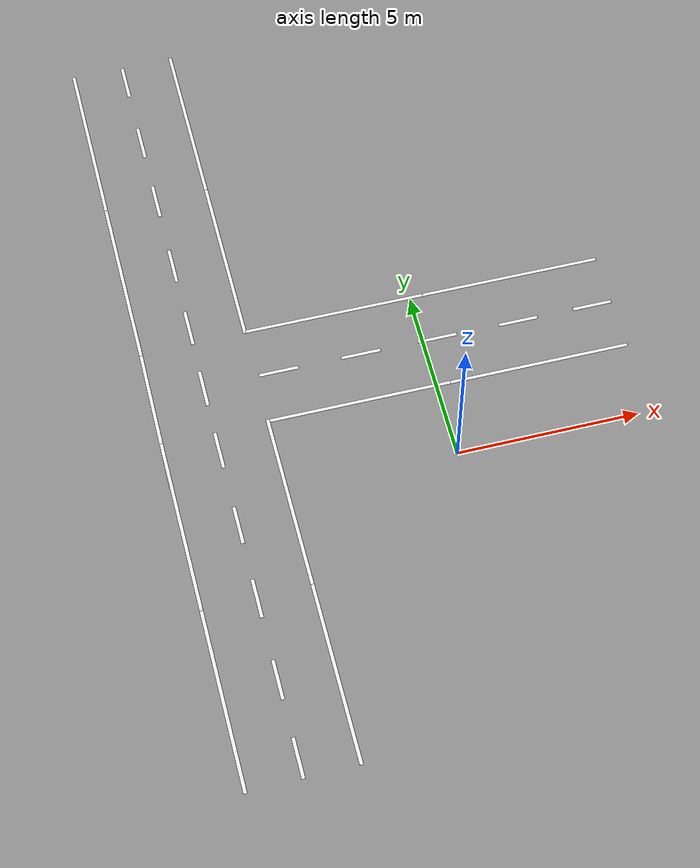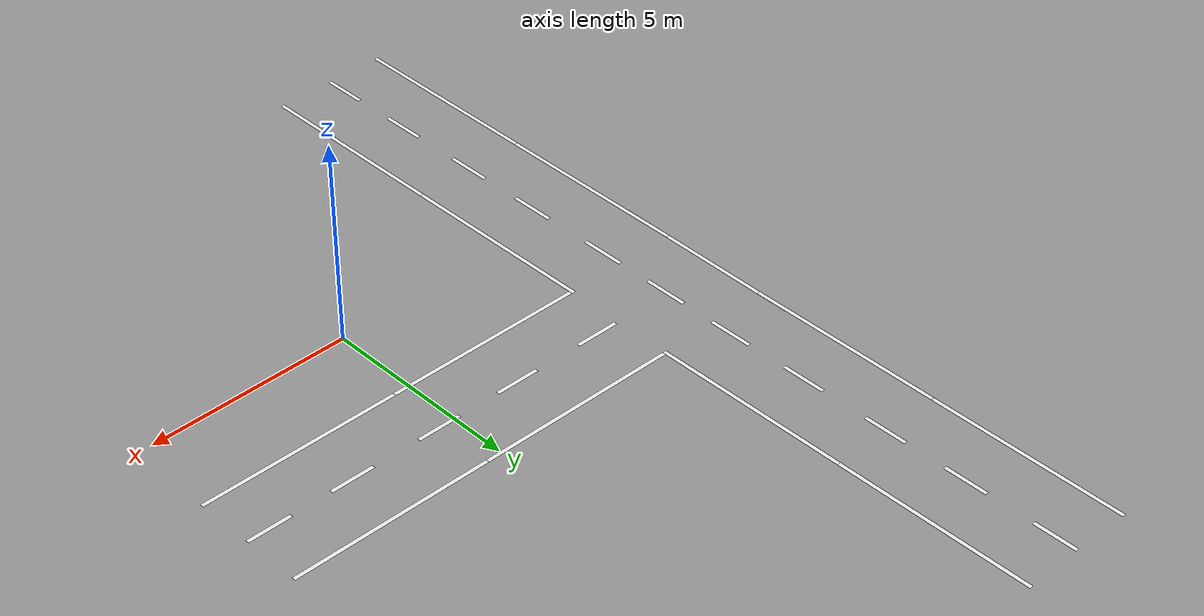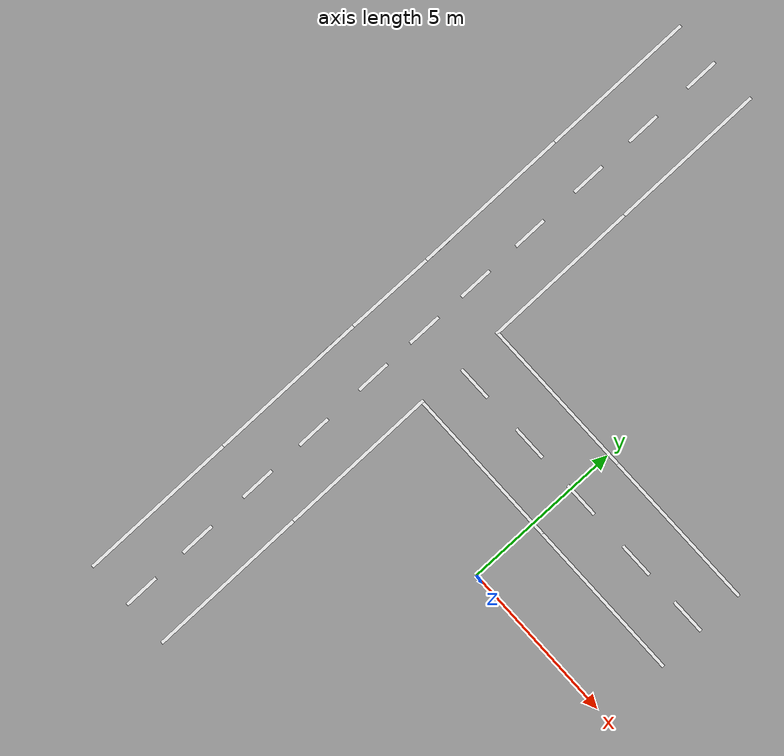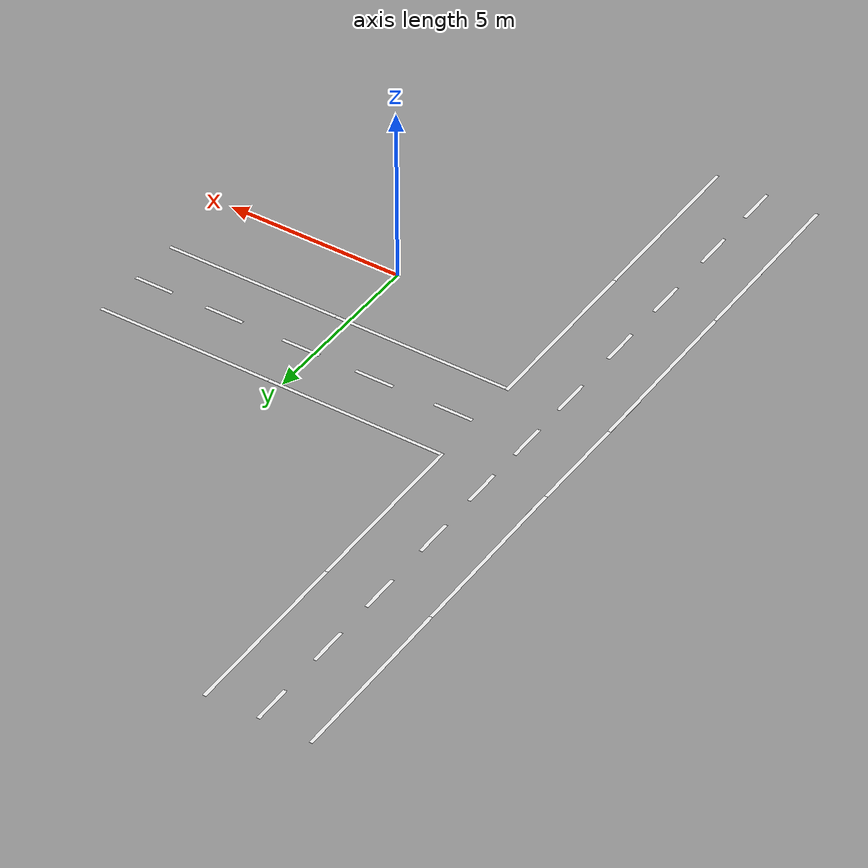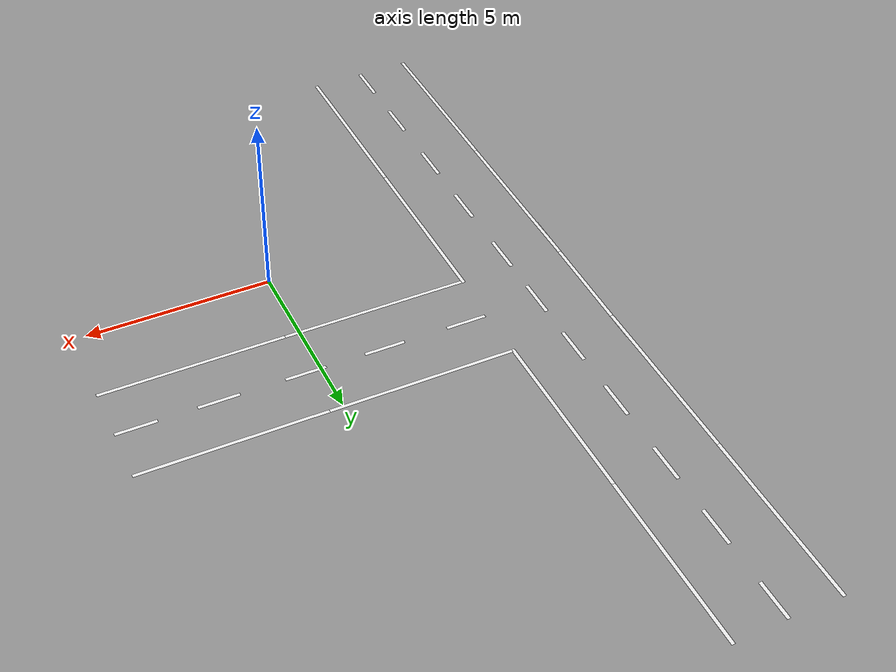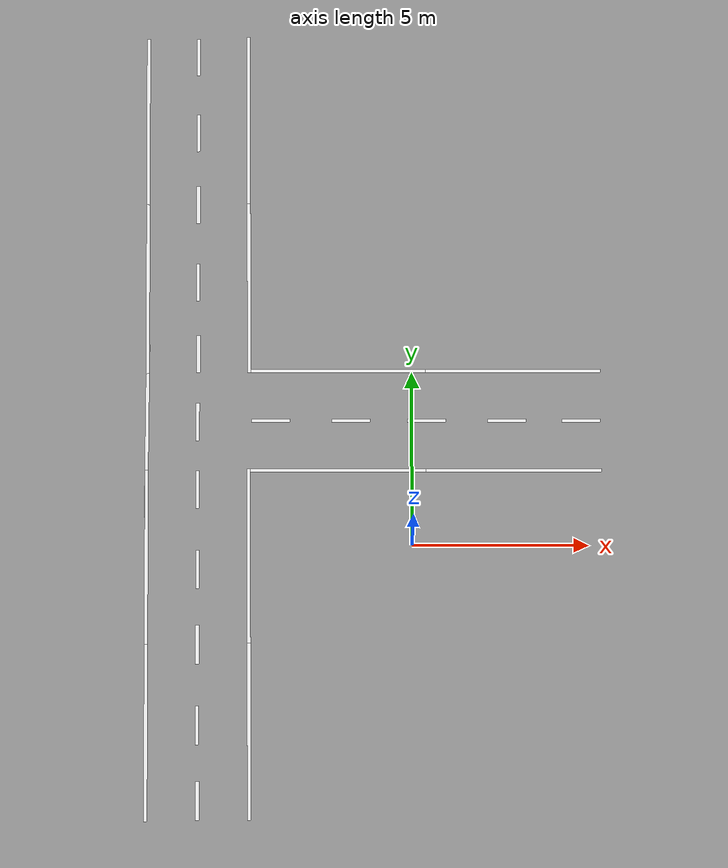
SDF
<?xml version='1.0'?>
<sdf version='1.6'>
  <model name='roadSystem'>
    <model name='road'>
      <model name='road'>
        <link name='link'>
          <pose frame=''>-0.42356 2.05106 0 0 -0 0</pose>
          <inertial>
            <mass>0.362604</mass>
            <inertia>
              <ixx>0.00016034</ixx>
              <ixy>0</ixy>
              <ixz>0</ixz>
              <iyy>0.757889</iyy>
              <iyz>0</iyz>
              <izz>0.758045</izz>
            </inertia>
            <pose frame=''>0 0 0 0 -0 0</pose>
          </inertial>
          <self_collide>0</self_collide>
          <kinematic>0</kinematic>
          <gravity>1</gravity>
          <visual name='visual'>
            <geometry>
              <box>
                <size>5 0.1 1e-06</size>
              </box>
            </geometry>
            <material>
              <script>
                <name>Gazebo/White</name>
                <uri>file://media/materials/scripts/gazebo.material</uri>
              </script>
              <shader type='pixel'>
                <normal_map>__default__</normal_map>
              </shader>
              <ambient>1 1 1 1</ambient>
              <diffuse>0.7 0.7 0.7 0</diffuse>
              <specular>0.01 0.01 0.01 0</specular>
              <emissive>0 0 0 1</emissive>
              <lighting>0</lighting>
            </material>
            <pose frame=''>0 0 0 0 -0 0</pose>
            <transparency>0</transparency>
            <cast_shadows>1</cast_shadows>
          </visual>
          <collision name='collision'>
            <laser_retro>0</laser_retro>
            <max_contacts>10</max_contacts>
            <pose frame=''>0 0 0 0 -0 0</pose>
            <geometry>
              <box>
                <size>5.00814 0.072377 0.008224</size>
              </box>
            </geometry>
            <surface>
              <friction>
                <ode>
                  <mu>1</mu>
                  <mu2>1</mu2>
                  <fdir1>0 0 0</fdir1>
                  <slip1>0</slip1>
                  <slip2>0</slip2>
                </ode>
                <torsional>
                  <coefficient>1</coefficient>
                  <patch_radius>0</patch_radius>
                  <surface_radius>0</surface_radius>
                  <use_patch_radius>1</use_patch_radius>
                  <ode>
                    <slip>0</slip>
                  </ode>
                </torsional>
              </friction>
              <bounce>
                <restitution_coefficient>0</restitution_coefficient>
                <threshold>1e+06</threshold>
              </bounce>
              <contact>
                <collide_without_contact>0</collide_without_contact>
                <collide_without_contact_bitmask>1</collide_without_contact_bitmask>
                <collide_bitmask>1</collide_bitmask>
                <ode>
                  <soft_cfm>0</soft_cfm>
                  <soft_erp>0.2</soft_erp>
                  <kp>1e+13</kp>
                  <kd>1</kd>
                  <max_vel>0.01</max_vel>
                  <min_depth>0</min_depth>
                </ode>
                <bullet>
                  <split_impulse>1</split_impulse>
                  <split_impulse_penetration_threshold>-0.01</split_impulse_penetration_threshold>
                  <soft_cfm>0</soft_cfm>
                  <soft_erp>0.2</soft_erp>
                  <kp>1e+13</kp>
                  <kd>1</kd>
                </bullet>
              </contact>
            </surface>
          </collision>
        </link>
        <static>0</static>
        <allow_auto_disable>1</allow_auto_disable>
        <pose frame=''>4.98271 0.008236 0 0 -0 0</pose>
      </model>
      <model name='road_clone'>
        <link name='link'>
          <pose frame=''>-0.42356 2.05106 0 0 -0 0</pose>
          <inertial>
            <mass>0.362604</mass>
            <inertia>
              <ixx>0.00016034</ixx>
              <ixy>0</ixy>
              <ixz>0</ixz>
              <iyy>0.757889</iyy>
              <iyz>0</iyz>
              <izz>0.758045</izz>
            </inertia>
            <pose frame=''>0 0 0 0 -0 0</pose>
          </inertial>
          <self_collide>0</self_collide>
          <kinematic>0</kinematic>
          <gravity>1</gravity>
          <visual name='visual'>
            <geometry>
              <box>
                <size>5 0.1 1e-06</size>
              </box>
            </geometry>
            <material>
              <script>
                <name>Gazebo/White</name>
                <uri>file://media/materials/scripts/gazebo.material</uri>
              </script>
              <shader type='pixel'>
                <normal_map>__default__</normal_map>
              </shader>
              <ambient>1 1 1 1</ambient>
              <diffuse>0.7 0.7 0.7 0</diffuse>
              <specular>0.01 0.01 0.01 0</specular>
              <emissive>0 0 0 1</emissive>
              <lighting>0</lighting>
            </material>
            <pose frame=''>0 0 0 0 -0 0</pose>
            <transparency>0</transparency>
            <cast_shadows>1</cast_shadows>
          </visual>
          <collision name='collision'>
            <laser_retro>0</laser_retro>
            <max_contacts>10</max_contacts>
            <pose frame=''>0 0 0 0 -0 0</pose>
            <geometry>
              <box>
                <size>5.00814 0.072377 0.008224</size>
              </box>
            </geometry>
            <surface>
              <friction>
                <ode>
                  <mu>1</mu>
                  <mu2>1</mu2>
                  <fdir1>0 0 0</fdir1>
                  <slip1>0</slip1>
                  <slip2>0</slip2>
                </ode>
                <torsional>
                  <coefficient>1</coefficient>
                  <patch_radius>0</patch_radius>
                  <surface_radius>0</surface_radius>
                  <use_patch_radius>1</use_patch_radius>
                  <ode>
                    <slip>0</slip>
                  </ode>
                </torsional>
              </friction>
              <bounce>
                <restitution_coefficient>0</restitution_coefficient>
                <threshold>1e+06</threshold>
              </bounce>
              <contact>
                <collide_without_contact>0</collide_without_contact>
                <collide_without_contact_bitmask>1</collide_without_contact_bitmask>
                <collide_bitmask>1</collide_bitmask>
                <ode>
                  <soft_cfm>0</soft_cfm>
                  <soft_erp>0.2</soft_erp>
                  <kp>1e+13</kp>
                  <kd>1</kd>
                  <max_vel>0.01</max_vel>
                  <min_depth>0</min_depth>
                </ode>
                <bullet>
                  <split_impulse>1</split_impulse>
                  <split_impulse_penetration_threshold>-0.01</split_impulse_penetration_threshold>
                  <soft_cfm>0</soft_cfm>
                  <soft_erp>0.2</soft_erp>
                  <kp>1e+13</kp>
                  <kd>1</kd>
                </bullet>
              </contact>
            </surface>
          </collision>
        </link>
        <static>0</static>
        <allow_auto_disable>1</allow_auto_disable>
        <pose frame=''>-0.01634 0.008315 0 0 -0 0</pose>
      </model>
      <model name='roadmark'>
        <link name='link'>
          <pose frame=''>-0.38042 1.1429 0 0 -0 0</pose>
          <inertial>
            <mass>0.362604</mass>
            <inertia>
              <ixx>0.00016034</ixx>
              <ixy>0</ixy>
              <ixz>0</ixz>
              <iyy>0.757889</iyy>
              <iyz>0</iyz>
              <izz>0.758045</izz>
            </inertia>
            <pose frame=''>0 0 0 0 -0 0</pose>
          </inertial>
          <self_collide>0</self_collide>
          <kinematic>0</kinematic>
          <gravity>1</gravity>
          <visual name='visual'>
            <geometry>
              <box>
                <size>5 0.1 1e-06</size>
              </box>
            </geometry>
            <material>
              <script>
                <name>Gazebo/White</name>
                <uri>file://media/materials/scripts/gazebo.material</uri>
              </script>
              <shader type='pixel'>
                <normal_map>__default__</normal_map>
              </shader>
              <ambient>1 1 1 1</ambient>
              <diffuse>0.7 0.7 0.7 0</diffuse>
              <specular>0.01 0.01 0.01 0</specular>
              <emissive>0 0 0 1</emissive>
              <lighting>0</lighting>
            </material>
            <pose frame=''>0 0 0 0 -0 0</pose>
            <transparency>0</transparency>
            <cast_shadows>1</cast_shadows>
          </visual>
          <collision name='collision'>
            <laser_retro>0</laser_retro>
            <max_contacts>10</max_contacts>
            <pose frame=''>0 0 0 0 -0 0</pose>
            <geometry>
              <box>
                <size>5.00814 0.072377 0.008224</size>
              </box>
            </geometry>
            <surface>
              <friction>
                <ode>
                  <mu>1</mu>
                  <mu2>1</mu2>
                  <fdir1>0 0 0</fdir1>
                  <slip1>0</slip1>
                  <slip2>0</slip2>
                </ode>
                <torsional>
                  <coefficient>1</coefficient>
                  <patch_radius>0</patch_radius>
                  <surface_radius>0</surface_radius>
                  <use_patch_radius>1</use_patch_radius>
                  <ode>
                    <slip>0</slip>
                  </ode>
                </torsional>
              </friction>
              <bounce>
                <restitution_coefficient>0</restitution_coefficient>
                <threshold>1e+06</threshold>
              </bounce>
              <contact>
                <collide_without_contact>0</collide_without_contact>
                <collide_without_contact_bitmask>1</collide_without_contact_bitmask>
                <collide_bitmask>1</collide_bitmask>
                <ode>
                  <soft_cfm>0</soft_cfm>
                  <soft_erp>0.2</soft_erp>
                  <kp>1e+13</kp>
                  <kd>1</kd>
                  <max_vel>0.01</max_vel>
                  <min_depth>0</min_depth>
                </ode>
                <bullet>
                  <split_impulse>1</split_impulse>
                  <split_impulse_penetration_threshold>-0.01</split_impulse_penetration_threshold>
                  <soft_cfm>0</soft_cfm>
                  <soft_erp>0.2</soft_erp>
                  <kp>1e+13</kp>
                  <kd>1</kd>
                </bullet>
              </contact>
            </surface>
          </collision>
        </link>
        <static>0</static>
        <allow_auto_disable>1</allow_auto_disable>
        <pose frame=''>-0.037207 -1.98082 0 0 -0 0</pose>
      </model>
      <model name='roadmark_clone_0'>
        <link name='link'>
          <pose frame=''>-0.38042 1.1429 0 0 -0 0</pose>
          <inertial>
            <mass>0.362604</mass>
            <inertia>
              <ixx>0.00016034</ixx>
              <ixy>0</ixy>
              <ixz>0</ixz>
              <iyy>0.757889</iyy>
              <iyz>0</iyz>
              <izz>0.758045</izz>
            </inertia>
            <pose frame=''>0 0 0 0 -0 0</pose>
          </inertial>
          <self_collide>0</self_collide>
          <kinematic>0</kinematic>
          <gravity>1</gravity>
          <visual name='visual'>
            <geometry>
              <box>
                <size>5 0.1 1e-06</size>
              </box>
            </geometry>
            <material>
              <script>
                <name>Gazebo/White</name>
                <uri>file://media/materials/scripts/gazebo.material</uri>
              </script>
              <shader type='pixel'>
                <normal_map>__default__</normal_map>
              </shader>
              <ambient>1 1 1 1</ambient>
              <diffuse>0.7 0.7 0.7 0</diffuse>
              <specular>0.01 0.01 0.01 0</specular>
              <emissive>0 0 0 1</emissive>
              <lighting>0</lighting>
            </material>
            <pose frame=''>0 0 0 0 -0 0</pose>
            <transparency>0</transparency>
            <cast_shadows>1</cast_shadows>
          </visual>
          <collision name='collision'>
            <laser_retro>0</laser_retro>
            <max_contacts>10</max_contacts>
            <pose frame=''>0 0 0 0 -0 0</pose>
            <geometry>
              <box>
                <size>5.00814 0.072377 0.008224</size>
              </box>
            </geometry>
            <surface>
              <friction>
                <ode>
                  <mu>1</mu>
                  <mu2>1</mu2>
                  <fdir1>0 0 0</fdir1>
                  <slip1>0</slip1>
                  <slip2>0</slip2>
                </ode>
                <torsional>
                  <coefficient>1</coefficient>
                  <patch_radius>0</patch_radius>
                  <surface_radius>0</surface_radius>
                  <use_patch_radius>1</use_patch_radius>
                  <ode>
                    <slip>0</slip>
                  </ode>
                </torsional>
              </friction>
              <bounce>
                <restitution_coefficient>0</restitution_coefficient>
                <threshold>1e+06</threshold>
              </bounce>
              <contact>
                <collide_without_contact>0</collide_without_contact>
                <collide_without_contact_bitmask>1</collide_without_contact_bitmask>
                <collide_bitmask>1</collide_bitmask>
                <ode>
                  <soft_cfm>0</soft_cfm>
                  <soft_erp>0.2</soft_erp>
                  <kp>1e+13</kp>
                  <kd>1</kd>
                  <max_vel>0.01</max_vel>
                  <min_depth>0</min_depth>
                </ode>
                <bullet>
                  <split_impulse>1</split_impulse>
                  <split_impulse_penetration_threshold>-0.01</split_impulse_penetration_threshold>
                  <soft_cfm>0</soft_cfm>
                  <soft_erp>0.2</soft_erp>
                  <kp>1e+13</kp>
                  <kd>1</kd>
                </bullet>
              </contact>
            </surface>
          </collision>
        </link>
        <static>0</static>
        <allow_auto_disable>1</allow_auto_disable>
        <pose frame=''>4.94295 -1.98208 0 0 -0 0</pose>
      </model>
      <model name='roadmark_mid'>
        <link name='link'>
          <pose frame=''>-2.29682 2.593 0.0001 0 -0 0</pose>
          <inertial>
            <mass>0.0807885</mass>
            <inertia>
              <ixx>3.572e-05</ixx>
              <ixy>0</ixy>
              <ixz>0</ixz>
              <iyy>0.00838261</iyy>
              <iyz>0</iyz>
              <izz>0.00841742</izz>
            </inertia>
            <pose frame=''>0 0 0 0 -0 0</pose>
          </inertial>
          <self_collide>0</self_collide>
          <kinematic>0</kinematic>
          <visual name='visual'>
            <geometry>
              <box>
                <size>1.1 0.1 1e-06</size>
              </box>
            </geometry>
            <material>
              <script>
                <name>Gazebo/White</name>
                <uri>file://media/materials/scripts/gazebo.material</uri>
              </script>
              <shader type='pixel'>
                <normal_map>__default__</normal_map>
              </shader>
              <ambient>1 1 1 1</ambient>
              <diffuse>0.7 0.7 0.7 0</diffuse>
              <specular>0.01 0.01 0.01 0</specular>
              <emissive>0 0 0 1</emissive>
              <lighting>0</lighting>
            </material>
            <pose frame=''>0 0 0 0 -0 0</pose>
            <transparency>0</transparency>
            <cast_shadows>1</cast_shadows>
          </visual>
          <collision name='collision'>
            <laser_retro>0</laser_retro>
            <max_contacts>10</max_contacts>
            <pose frame=''>0 0 0 0 -0 0</pose>
            <geometry>
              <box>
                <size>1.11582 0.072377 0.008224</size>
              </box>
            </geometry>
            <surface>
              <friction>
                <ode>
                  <mu>1</mu>
                  <mu2>1</mu2>
                  <fdir1>0 0 0</fdir1>
                  <slip1>0</slip1>
                  <slip2>0</slip2>
                </ode>
                <torsional>
                  <coefficient>1</coefficient>
                  <patch_radius>0</patch_radius>
                  <surface_radius>0</surface_radius>
                  <use_patch_radius>1</use_patch_radius>
                  <ode>
                    <slip>0</slip>
                  </ode>
                </torsional>
              </friction>
              <bounce>
                <restitution_coefficient>0</restitution_coefficient>
                <threshold>1e+06</threshold>
              </bounce>
              <contact>
                <collide_without_contact>0</collide_without_contact>
                <collide_without_contact_bitmask>1</collide_without_contact_bitmask>
                <collide_bitmask>1</collide_bitmask>
                <ode>
                  <soft_cfm>0</soft_cfm>
                  <soft_erp>0.2</soft_erp>
                  <kp>1e+13</kp>
                  <kd>1</kd>
                  <max_vel>0.01</max_vel>
                  <min_depth>0</min_depth>
                </ode>
                <bullet>
                  <split_impulse>1</split_impulse>
                  <split_impulse_penetration_threshold>-0.01</split_impulse_penetration_threshold>
                  <soft_cfm>0</soft_cfm>
                  <soft_erp>0.2</soft_erp>
                  <kp>1e+13</kp>
                  <kd>1</kd>
                </bullet>
              </contact>
            </surface>
          </collision>
        </link>
        <static>0</static>
        <allow_auto_disable>1</allow_auto_disable>
        <pose frame=''>8.80135 -1.98422 0 0 -0 0</pose>
      </model>
      <model name='roadmark_mid_clone'>
        <link name='link'>
          <pose frame=''>-2.29682 2.593 0.0001 0 -0 0</pose>
          <inertial>
            <mass>0.0807885</mass>
            <inertia>
              <ixx>3.572e-05</ixx>
              <ixy>0</ixy>
              <ixz>0</ixz>
              <iyy>0.00838261</iyy>
              <iyz>0</iyz>
              <izz>0.00841742</izz>
            </inertia>
            <pose frame=''>0 0 0 0 -0 0</pose>
          </inertial>
          <self_collide>0</self_collide>
          <kinematic>0</kinematic>
          <visual name='visual'>
            <geometry>
              <box>
                <size>1.1 0.1 1e-06</size>
              </box>
            </geometry>
            <material>
              <script>
                <name>Gazebo/White</name>
                <uri>file://media/materials/scripts/gazebo.material</uri>
              </script>
              <shader type='pixel'>
                <normal_map>__default__</normal_map>
              </shader>
              <ambient>1 1 1 1</ambient>
              <diffuse>0.7 0.7 0.7 0</diffuse>
              <specular>0.01 0.01 0.01 0</specular>
              <emissive>0 0 0 1</emissive>
              <lighting>0</lighting>
            </material>
            <pose frame=''>0 0 0 0 -0 0</pose>
            <transparency>0</transparency>
            <cast_shadows>1</cast_shadows>
          </visual>
          <collision name='collision'>
            <laser_retro>0</laser_retro>
            <max_contacts>10</max_contacts>
            <pose frame=''>0 0 0 0 -0 0</pose>
            <geometry>
              <box>
                <size>1.11582 0.072377 0.008224</size>
              </box>
            </geometry>
            <surface>
              <friction>
                <ode>
                  <mu>1</mu>
                  <mu2>1</mu2>
                  <fdir1>0 0 0</fdir1>
                  <slip1>0</slip1>
                  <slip2>0</slip2>
                </ode>
                <torsional>
                  <coefficient>1</coefficient>
                  <patch_radius>0</patch_radius>
                  <surface_radius>0</surface_radius>
                  <use_patch_radius>1</use_patch_radius>
                  <ode>
                    <slip>0</slip>
                  </ode>
                </torsional>
              </friction>
              <bounce>
                <restitution_coefficient>0</restitution_coefficient>
                <threshold>1e+06</threshold>
              </bounce>
              <contact>
                <collide_without_contact>0</collide_without_contact>
                <collide_without_contact_bitmask>1</collide_without_contact_bitmask>
                <collide_bitmask>1</collide_bitmask>
                <ode>
                  <soft_cfm>0</soft_cfm>
                  <soft_erp>0.2</soft_erp>
                  <kp>1e+13</kp>
                  <kd>1</kd>
                  <max_vel>0.01</max_vel>
                  <min_depth>0</min_depth>
                </ode>
                <bullet>
                  <split_impulse>1</split_impulse>
                  <split_impulse_penetration_threshold>-0.01</split_impulse_penetration_threshold>
                  <soft_cfm>0</soft_cfm>
                  <soft_erp>0.2</soft_erp>
                  <kp>1e+13</kp>
                  <kd>1</kd>
                </bullet>
              </contact>
            </surface>
          </collision>
        </link>
        <static>0</static>
        <allow_auto_disable>1</allow_auto_disable>
        <pose frame=''>-0.048046 -1.98463 0 0 -0 0</pose>
      </model>
      <model name='roadmark_mid_clone_0'>
        <link name='link'>
          <pose frame=''>-2.29682 2.593 0.0001 0 -0 0</pose>
          <inertial>
            <mass>0.0807885</mass>
            <inertia>
              <ixx>3.572e-05</ixx>
              <ixy>0</ixy>
              <ixz>0</ixz>
              <iyy>0.00838261</iyy>
              <iyz>0</iyz>
              <izz>0.00841742</izz>
            </inertia>
            <pose frame=''>0 0 0 0 -0 0</pose>
          </inertial>
          <self_collide>0</self_collide>
          <kinematic>0</kinematic>
          <visual name='visual'>
            <geometry>
              <box>
                <size>1.1 0.1 1e-06</size>
              </box>
            </geometry>
            <material>
              <script>
                <name>Gazebo/White</name>
                <uri>file://media/materials/scripts/gazebo.material</uri>
              </script>
              <shader type='pixel'>
                <normal_map>__default__</normal_map>
              </shader>
              <ambient>1 1 1 1</ambient>
              <diffuse>0.7 0.7 0.7 0</diffuse>
              <specular>0.01 0.01 0.01 0</specular>
              <emissive>0 0 0 1</emissive>
              <lighting>0</lighting>
            </material>
            <pose frame=''>0 0 0 0 -0 0</pose>
            <transparency>0</transparency>
            <cast_shadows>1</cast_shadows>
          </visual>
          <collision name='collision'>
            <laser_retro>0</laser_retro>
            <max_contacts>10</max_contacts>
            <pose frame=''>0 0 0 0 -0 0</pose>
            <geometry>
              <box>
                <size>1.11582 0.072377 0.008224</size>
              </box>
            </geometry>
            <surface>
              <friction>
                <ode>
                  <mu>1</mu>
                  <mu2>1</mu2>
                  <fdir1>0 0 0</fdir1>
                  <slip1>0</slip1>
                  <slip2>0</slip2>
                </ode>
                <torsional>
                  <coefficient>1</coefficient>
                  <patch_radius>0</patch_radius>
                  <surface_radius>0</surface_radius>
                  <use_patch_radius>1</use_patch_radius>
                  <ode>
                    <slip>0</slip>
                  </ode>
                </torsional>
              </friction>
              <bounce>
                <restitution_coefficient>0</restitution_coefficient>
                <threshold>1e+06</threshold>
              </bounce>
              <contact>
                <collide_without_contact>0</collide_without_contact>
                <collide_without_contact_bitmask>1</collide_without_contact_bitmask>
                <collide_bitmask>1</collide_bitmask>
                <ode>
                  <soft_cfm>0</soft_cfm>
                  <soft_erp>0.2</soft_erp>
                  <kp>1e+13</kp>
                  <kd>1</kd>
                  <max_vel>0.01</max_vel>
                  <min_depth>0</min_depth>
                </ode>
                <bullet>
                  <split_impulse>1</split_impulse>
                  <split_impulse_penetration_threshold>-0.01</split_impulse_penetration_threshold>
                  <soft_cfm>0</soft_cfm>
                  <soft_erp>0.2</soft_erp>
                  <kp>1e+13</kp>
                  <kd>1</kd>
                </bullet>
              </contact>
            </surface>
          </collision>
        </link>
        <static>0</static>
        <allow_auto_disable>1</allow_auto_disable>
        <pose frame=''>4.39245 -1.98631 0 0 -0 0</pose>
      </model>
      <model name='roadmark_mid_clone_1'>
        <link name='link'>
          <pose frame=''>-2.29682 2.593 0.0001 0 -0 0</pose>
          <inertial>
            <mass>0.0807885</mass>
            <inertia>
              <ixx>3.572e-05</ixx>
              <ixy>0</ixy>
              <ixz>0</ixz>
              <iyy>0.00838261</iyy>
              <iyz>0</iyz>
              <izz>0.00841742</izz>
            </inertia>
            <pose frame=''>0 0 0 0 -0 0</pose>
          </inertial>
          <self_collide>0</self_collide>
          <kinematic>0</kinematic>
          <visual name='visual'>
            <geometry>
              <box>
                <size>1.1 0.1 1e-06</size>
              </box>
            </geometry>
            <material>
              <script>
                <name>Gazebo/White</name>
                <uri>file://media/materials/scripts/gazebo.material</uri>
              </script>
              <shader type='pixel'>
                <normal_map>__default__</normal_map>
              </shader>
              <ambient>1 1 1 1</ambient>
              <diffuse>0.7 0.7 0.7 0</diffuse>
              <specular>0.01 0.01 0.01 0</specular>
              <emissive>0 0 0 1</emissive>
              <lighting>0</lighting>
            </material>
            <pose frame=''>0 0 0 0 -0 0</pose>
            <transparency>0</transparency>
            <cast_shadows>1</cast_shadows>
          </visual>
          <collision name='collision'>
            <laser_retro>0</laser_retro>
            <max_contacts>10</max_contacts>
            <pose frame=''>0 0 0 0 -0 0</pose>
            <geometry>
              <box>
                <size>1.11582 0.072377 0.008224</size>
              </box>
            </geometry>
            <surface>
              <friction>
                <ode>
                  <mu>1</mu>
                  <mu2>1</mu2>
                  <fdir1>0 0 0</fdir1>
                  <slip1>0</slip1>
                  <slip2>0</slip2>
                </ode>
                <torsional>
                  <coefficient>1</coefficient>
                  <patch_radius>0</patch_radius>
                  <surface_radius>0</surface_radius>
                  <use_patch_radius>1</use_patch_radius>
                  <ode>
                    <slip>0</slip>
                  </ode>
                </torsional>
              </friction>
              <bounce>
                <restitution_coefficient>0</restitution_coefficient>
                <threshold>1e+06</threshold>
              </bounce>
              <contact>
                <collide_without_contact>0</collide_without_contact>
                <collide_without_contact_bitmask>1</collide_without_contact_bitmask>
                <collide_bitmask>1</collide_bitmask>
                <ode>
                  <soft_cfm>0</soft_cfm>
                  <soft_erp>0.2</soft_erp>
                  <kp>1e+13</kp>
                  <kd>1</kd>
                  <max_vel>0.01</max_vel>
                  <min_depth>0</min_depth>
                </ode>
                <bullet>
                  <split_impulse>1</split_impulse>
                  <split_impulse_penetration_threshold>-0.01</split_impulse_penetration_threshold>
                  <soft_cfm>0</soft_cfm>
                  <soft_erp>0.2</soft_erp>
                  <kp>1e+13</kp>
                  <kd>1</kd>
                </bullet>
              </contact>
            </surface>
          </collision>
        </link>
        <static>0</static>
        <allow_auto_disable>1</allow_auto_disable>
        <pose frame=''>6.68356 -1.98916 0 0 -0 0</pose>
      </model>
      <model name='roadmark_mid_clone_2'>
        <link name='link'>
          <pose frame=''>-2.29682 2.593 0.0001 0 -0 0</pose>
          <inertial>
            <mass>0.0807885</mass>
            <inertia>
              <ixx>3.572e-05</ixx>
              <ixy>0</ixy>
              <ixz>0</ixz>
              <iyy>0.00838261</iyy>
              <iyz>0</iyz>
              <izz>0.00841742</izz>
            </inertia>
            <pose frame=''>0 0 0 0 -0 0</pose>
          </inertial>
          <self_collide>0</self_collide>
          <kinematic>0</kinematic>
          <visual name='visual'>
            <geometry>
              <box>
                <size>1.1 0.1 1e-06</size>
              </box>
            </geometry>
            <material>
              <script>
                <name>Gazebo/White</name>
                <uri>file://media/materials/scripts/gazebo.material</uri>
              </script>
              <shader type='pixel'>
                <normal_map>__default__</normal_map>
              </shader>
              <ambient>1 1 1 1</ambient>
              <diffuse>0.7 0.7 0.7 0</diffuse>
              <specular>0.01 0.01 0.01 0</specular>
              <emissive>0 0 0 1</emissive>
              <lighting>0</lighting>
            </material>
            <pose frame=''>0 0 0 0 -0 0</pose>
            <transparency>0</transparency>
            <cast_shadows>1</cast_shadows>
          </visual>
          <collision name='collision'>
            <laser_retro>0</laser_retro>
            <max_contacts>10</max_contacts>
            <pose frame=''>0 0 0 0 -0 0</pose>
            <geometry>
              <box>
                <size>1.11582 0.072377 0.008224</size>
              </box>
            </geometry>
            <surface>
              <friction>
                <ode>
                  <mu>1</mu>
                  <mu2>1</mu2>
                  <fdir1>0 0 0</fdir1>
                  <slip1>0</slip1>
                  <slip2>0</slip2>
                </ode>
                <torsional>
                  <coefficient>1</coefficient>
                  <patch_radius>0</patch_radius>
                  <surface_radius>0</surface_radius>
                  <use_patch_radius>1</use_patch_radius>
                  <ode>
                    <slip>0</slip>
                  </ode>
                </torsional>
              </friction>
              <bounce>
                <restitution_coefficient>0</restitution_coefficient>
                <threshold>1e+06</threshold>
              </bounce>
              <contact>
                <collide_without_contact>0</collide_without_contact>
                <collide_without_contact_bitmask>1</collide_without_contact_bitmask>
                <collide_bitmask>1</collide_bitmask>
                <ode>
                  <soft_cfm>0</soft_cfm>
                  <soft_erp>0.2</soft_erp>
                  <kp>1e+13</kp>
                  <kd>1</kd>
                  <max_vel>0.01</max_vel>
                  <min_depth>0</min_depth>
                </ode>
                <bullet>
                  <split_impulse>1</split_impulse>
                  <split_impulse_penetration_threshold>-0.01</split_impulse_penetration_threshold>
                  <soft_cfm>0</soft_cfm>
                  <soft_erp>0.2</soft_erp>
                  <kp>1e+13</kp>
                  <kd>1</kd>
                </bullet>
              </contact>
            </surface>
          </collision>
        </link>
        <static>0</static>
        <allow_auto_disable>1</allow_auto_disable>
        <pose frame=''>2.24236 -1.98333 0 0 -0 0</pose>
      </model>
      <static>0</static>
      <allow_auto_disable>1</allow_auto_disable>
      <pose frame=''>-1.68364 3.00119 0.008097 -0 -0 -0</pose>
    </model>
    <model name='road_clone'>
      <model name='road'>
        <link name='link'>
          <pose frame=''>-0.42356 2.05106 0 0 -0 0</pose>
          <inertial>
            <mass>0.362604</mass>
            <inertia>
              <ixx>0.00016034</ixx>
              <ixy>0</ixy>
              <ixz>0</ixz>
              <iyy>0.757889</iyy>
              <iyz>0</iyz>
              <izz>0.758045</izz>
            </inertia>
            <pose frame=''>0 0 0 0 -0 0</pose>
          </inertial>
          <self_collide>0</self_collide>
          <kinematic>0</kinematic>
          <gravity>1</gravity>
          <visual name='visual'>
            <geometry>
              <box>
                <size>5 0.1 1e-06</size>
              </box>
            </geometry>
            <material>
              <script>
                <name>Gazebo/White</name>
                <uri>file://media/materials/scripts/gazebo.material</uri>
              </script>
              <shader type='pixel'>
                <normal_map>__default__</normal_map>
              </shader>
              <ambient>1 1 1 1</ambient>
              <diffuse>0.7 0.7 0.7 0</diffuse>
              <specular>0.01 0.01 0.01 0</specular>
              <emissive>0 0 0 1</emissive>
              <lighting>0</lighting>
            </material>
            <pose frame=''>0 0 0 0 -0 0</pose>
            <transparency>0</transparency>
            <cast_shadows>1</cast_shadows>
          </visual>
          <collision name='collision'>
            <laser_retro>0</laser_retro>
            <max_contacts>10</max_contacts>
            <pose frame=''>0 0 0 0 -0 0</pose>
            <geometry>
              <box>
                <size>5.00814 0.072377 0.008224</size>
              </box>
            </geometry>
            <surface>
              <friction>
                <ode>
                  <mu>1</mu>
                  <mu2>1</mu2>
                  <fdir1>0 0 0</fdir1>
                  <slip1>0</slip1>
                  <slip2>0</slip2>
                </ode>
                <torsional>
                  <coefficient>1</coefficient>
                  <patch_radius>0</patch_radius>
                  <surface_radius>0</surface_radius>
                  <use_patch_radius>1</use_patch_radius>
                  <ode>
                    <slip>0</slip>
                  </ode>
                </torsional>
              </friction>
              <bounce>
                <restitution_coefficient>0</restitution_coefficient>
                <threshold>1e+06</threshold>
              </bounce>
              <contact>
                <collide_without_contact>0</collide_without_contact>
                <collide_without_contact_bitmask>1</collide_without_contact_bitmask>
                <collide_bitmask>1</collide_bitmask>
                <ode>
                  <soft_cfm>0</soft_cfm>
                  <soft_erp>0.2</soft_erp>
                  <kp>1e+13</kp>
                  <kd>1</kd>
                  <max_vel>0.01</max_vel>
                  <min_depth>0</min_depth>
                </ode>
                <bullet>
                  <split_impulse>1</split_impulse>
                  <split_impulse_penetration_threshold>-0.01</split_impulse_penetration_threshold>
                  <soft_cfm>0</soft_cfm>
                  <soft_erp>0.2</soft_erp>
                  <kp>1e+13</kp>
                  <kd>1</kd>
                </bullet>
              </contact>
            </surface>
          </collision>
        </link>
        <static>0</static>
        <allow_auto_disable>1</allow_auto_disable>
        <pose frame=''>4.98271 0.008236 0 0 -0 0</pose>
      </model>
      <model name='road_clone'>
        <link name='link'>
          <pose frame=''>-0.42356 2.05106 0 0 -0 0</pose>
          <inertial>
            <mass>0.362604</mass>
            <inertia>
              <ixx>0.00016034</ixx>
              <ixy>0</ixy>
              <ixz>0</ixz>
              <iyy>0.757889</iyy>
              <iyz>0</iyz>
              <izz>0.758045</izz>
            </inertia>
            <pose frame=''>0 0 0 0 -0 0</pose>
          </inertial>
          <self_collide>0</self_collide>
          <kinematic>0</kinematic>
          <gravity>1</gravity>
          <visual name='visual'>
            <geometry>
              <box>
                <size>5 0.1 1e-06</size>
              </box>
            </geometry>
            <material>
              <script>
                <name>Gazebo/White</name>
                <uri>file://media/materials/scripts/gazebo.material</uri>
              </script>
              <shader type='pixel'>
                <normal_map>__default__</normal_map>
              </shader>
              <ambient>1 1 1 1</ambient>
              <diffuse>0.7 0.7 0.7 0</diffuse>
              <specular>0.01 0.01 0.01 0</specular>
              <emissive>0 0 0 1</emissive>
              <lighting>0</lighting>
            </material>
            <pose frame=''>0 0 0 0 -0 0</pose>
            <transparency>0</transparency>
            <cast_shadows>1</cast_shadows>
          </visual>
          <collision name='collision'>
            <laser_retro>0</laser_retro>
            <max_contacts>10</max_contacts>
            <pose frame=''>0 0 0 0 -0 0</pose>
            <geometry>
              <box>
                <size>5.00814 0.072377 0.008224</size>
              </box>
            </geometry>
            <surface>
              <friction>
                <ode>
                  <mu>1</mu>
                  <mu2>1</mu2>
                  <fdir1>0 0 0</fdir1>
                  <slip1>0</slip1>
                  <slip2>0</slip2>
                </ode>
                <torsional>
                  <coefficient>1</coefficient>
                  <patch_radius>0</patch_radius>
                  <surface_radius>0</surface_radius>
                  <use_patch_radius>1</use_patch_radius>
                  <ode>
                    <slip>0</slip>
                  </ode>
                </torsional>
              </friction>
              <bounce>
                <restitution_coefficient>0</restitution_coefficient>
                <threshold>1e+06</threshold>
              </bounce>
              <contact>
                <collide_without_contact>0</collide_without_contact>
                <collide_without_contact_bitmask>1</collide_without_contact_bitmask>
                <collide_bitmask>1</collide_bitmask>
                <ode>
                  <soft_cfm>0</soft_cfm>
                  <soft_erp>0.2</soft_erp>
                  <kp>1e+13</kp>
                  <kd>1</kd>
                  <max_vel>0.01</max_vel>
                  <min_depth>0</min_depth>
                </ode>
                <bullet>
                  <split_impulse>1</split_impulse>
                  <split_impulse_penetration_threshold>-0.01</split_impulse_penetration_threshold>
                  <soft_cfm>0</soft_cfm>
                  <soft_erp>0.2</soft_erp>
                  <kp>1e+13</kp>
                  <kd>1</kd>
                </bullet>
              </contact>
            </surface>
          </collision>
        </link>
        <static>0</static>
        <allow_auto_disable>1</allow_auto_disable>
        <pose frame=''>-0.01634 0.008315 0 0 -0 0</pose>
      </model>
      <model name='roadmark'>
        <link name='link'>
          <pose frame=''>-0.38042 1.1429 0 0 -0 0</pose>
          <inertial>
            <mass>0.362604</mass>
            <inertia>
              <ixx>0.00016034</ixx>
              <ixy>0</ixy>
              <ixz>0</ixz>
              <iyy>0.757889</iyy>
              <iyz>0</iyz>
              <izz>0.758045</izz>
            </inertia>
            <pose frame=''>0 0 0 0 -0 0</pose>
          </inertial>
          <self_collide>0</self_collide>
          <kinematic>0</kinematic>
          <gravity>1</gravity>
          <visual name='visual'>
            <geometry>
              <box>
                <size>5 0.1 1e-06</size>
              </box>
            </geometry>
            <material>
              <script>
                <name>Gazebo/White</name>
                <uri>file://media/materials/scripts/gazebo.material</uri>
              </script>
              <shader type='pixel'>
                <normal_map>__default__</normal_map>
              </shader>
              <ambient>1 1 1 1</ambient>
              <diffuse>0.7 0.7 0.7 0</diffuse>
              <specular>0.01 0.01 0.01 0</specular>
              <emissive>0 0 0 1</emissive>
              <lighting>0</lighting>
            </material>
            <pose frame=''>0 0 0 0 -0 0</pose>
            <transparency>0</transparency>
            <cast_shadows>1</cast_shadows>
          </visual>
          <collision name='collision'>
            <laser_retro>0</laser_retro>
            <max_contacts>10</max_contacts>
            <pose frame=''>0 0 0 0 -0 0</pose>
            <geometry>
              <box>
                <size>5.00814 0.072377 0.008224</size>
              </box>
            </geometry>
            <surface>
              <friction>
                <ode>
                  <mu>1</mu>
                  <mu2>1</mu2>
                  <fdir1>0 0 0</fdir1>
                  <slip1>0</slip1>
                  <slip2>0</slip2>
                </ode>
                <torsional>
                  <coefficient>1</coefficient>
                  <patch_radius>0</patch_radius>
                  <surface_radius>0</surface_radius>
                  <use_patch_radius>1</use_patch_radius>
                  <ode>
                    <slip>0</slip>
                  </ode>
                </torsional>
              </friction>
              <bounce>
                <restitution_coefficient>0</restitution_coefficient>
                <threshold>1e+06</threshold>
              </bounce>
              <contact>
                <collide_without_contact>0</collide_without_contact>
                <collide_without_contact_bitmask>1</collide_without_contact_bitmask>
                <collide_bitmask>1</collide_bitmask>
                <ode>
                  <soft_cfm>0</soft_cfm>
                  <soft_erp>0.2</soft_erp>
                  <kp>1e+13</kp>
                  <kd>1</kd>
                  <max_vel>0.01</max_vel>
                  <min_depth>0</min_depth>
                </ode>
                <bullet>
                  <split_impulse>1</split_impulse>
                  <split_impulse_penetration_threshold>-0.01</split_impulse_penetration_threshold>
                  <soft_cfm>0</soft_cfm>
                  <soft_erp>0.2</soft_erp>
                  <kp>1e+13</kp>
                  <kd>1</kd>
                </bullet>
              </contact>
            </surface>
          </collision>
        </link>
        <static>0</static>
        <allow_auto_disable>1</allow_auto_disable>
        <pose frame=''>-0.037207 -1.98082 0 0 -0 0</pose>
      </model>
      <model name='roadmark_clone_0'>
        <link name='link'>
          <pose frame=''>-0.38042 1.1429 0 0 -0 0</pose>
          <inertial>
            <mass>0.362604</mass>
            <inertia>
              <ixx>0.00016034</ixx>
              <ixy>0</ixy>
              <ixz>0</ixz>
              <iyy>0.757889</iyy>
              <iyz>0</iyz>
              <izz>0.758045</izz>
            </inertia>
            <pose frame=''>0 0 0 0 -0 0</pose>
          </inertial>
          <self_collide>0</self_collide>
          <kinematic>0</kinematic>
          <gravity>1</gravity>
          <visual name='visual'>
            <geometry>
              <box>
                <size>5 0.1 1e-06</size>
              </box>
            </geometry>
            <material>
              <script>
                <name>Gazebo/White</name>
                <uri>file://media/materials/scripts/gazebo.material</uri>
              </script>
              <shader type='pixel'>
                <normal_map>__default__</normal_map>
              </shader>
              <ambient>1 1 1 1</ambient>
              <diffuse>0.7 0.7 0.7 0</diffuse>
              <specular>0.01 0.01 0.01 0</specular>
              <emissive>0 0 0 1</emissive>
              <lighting>0</lighting>
            </material>
            <pose frame=''>0 0 0 0 -0 0</pose>
            <transparency>0</transparency>
            <cast_shadows>1</cast_shadows>
          </visual>
          <collision name='collision'>
            <laser_retro>0</laser_retro>
            <max_contacts>10</max_contacts>
            <pose frame=''>0 0 0 0 -0 0</pose>
            <geometry>
              <box>
                <size>5.00814 0.072377 0.008224</size>
              </box>
            </geometry>
            <surface>
              <friction>
                <ode>
                  <mu>1</mu>
                  <mu2>1</mu2>
                  <fdir1>0 0 0</fdir1>
                  <slip1>0</slip1>
                  <slip2>0</slip2>
                </ode>
                <torsional>
                  <coefficient>1</coefficient>
                  <patch_radius>0</patch_radius>
                  <surface_radius>0</surface_radius>
                  <use_patch_radius>1</use_patch_radius>
                  <ode>
                    <slip>0</slip>
                  </ode>
                </torsional>
              </friction>
              <bounce>
                <restitution_coefficient>0</restitution_coefficient>
                <threshold>1e+06</threshold>
              </bounce>
              <contact>
                <collide_without_contact>0</collide_without_contact>
                <collide_without_contact_bitmask>1</collide_without_contact_bitmask>
                <collide_bitmask>1</collide_bitmask>
                <ode>
                  <soft_cfm>0</soft_cfm>
                  <soft_erp>0.2</soft_erp>
                  <kp>1e+13</kp>
                  <kd>1</kd>
                  <max_vel>0.01</max_vel>
                  <min_depth>0</min_depth>
                </ode>
                <bullet>
                  <split_impulse>1</split_impulse>
                  <split_impulse_penetration_threshold>-0.01</split_impulse_penetration_threshold>
                  <soft_cfm>0</soft_cfm>
                  <soft_erp>0.2</soft_erp>
                  <kp>1e+13</kp>
                  <kd>1</kd>
                </bullet>
              </contact>
            </surface>
          </collision>
        </link>
        <static>0</static>
        <allow_auto_disable>1</allow_auto_disable>
        <pose frame=''>4.94295 -1.98208 0 0 -0 0</pose>
      </model>
      <model name='roadmark_mid'>
        <link name='link'>
          <pose frame=''>-2.29682 2.593 0.0001 0 -0 0</pose>
          <inertial>
            <mass>0.0807885</mass>
            <inertia>
              <ixx>3.572e-05</ixx>
              <ixy>0</ixy>
              <ixz>0</ixz>
              <iyy>0.00838261</iyy>
              <iyz>0</iyz>
              <izz>0.00841742</izz>
            </inertia>
            <pose frame=''>0 0 0 0 -0 0</pose>
          </inertial>
          <self_collide>0</self_collide>
          <kinematic>0</kinematic>
          <visual name='visual'>
            <geometry>
              <box>
                <size>1.1 0.1 1e-06</size>
              </box>
            </geometry>
            <material>
              <script>
                <name>Gazebo/White</name>
                <uri>file://media/materials/scripts/gazebo.material</uri>
              </script>
              <shader type='pixel'>
                <normal_map>__default__</normal_map>
              </shader>
              <ambient>1 1 1 1</ambient>
              <diffuse>0.7 0.7 0.7 0</diffuse>
              <specular>0.01 0.01 0.01 0</specular>
              <emissive>0 0 0 1</emissive>
              <lighting>0</lighting>
            </material>
            <pose frame=''>0 0 0 0 -0 0</pose>
            <transparency>0</transparency>
            <cast_shadows>1</cast_shadows>
          </visual>
          <collision name='collision'>
            <laser_retro>0</laser_retro>
            <max_contacts>10</max_contacts>
            <pose frame=''>0 0 0 0 -0 0</pose>
            <geometry>
              <box>
                <size>1.11582 0.072377 0.008224</size>
              </box>
            </geometry>
            <surface>
              <friction>
                <ode>
                  <mu>1</mu>
                  <mu2>1</mu2>
                  <fdir1>0 0 0</fdir1>
                  <slip1>0</slip1>
                  <slip2>0</slip2>
                </ode>
                <torsional>
                  <coefficient>1</coefficient>
                  <patch_radius>0</patch_radius>
                  <surface_radius>0</surface_radius>
                  <use_patch_radius>1</use_patch_radius>
                  <ode>
                    <slip>0</slip>
                  </ode>
                </torsional>
              </friction>
              <bounce>
                <restitution_coefficient>0</restitution_coefficient>
                <threshold>1e+06</threshold>
              </bounce>
              <contact>
                <collide_without_contact>0</collide_without_contact>
                <collide_without_contact_bitmask>1</collide_without_contact_bitmask>
                <collide_bitmask>1</collide_bitmask>
                <ode>
                  <soft_cfm>0</soft_cfm>
                  <soft_erp>0.2</soft_erp>
                  <kp>1e+13</kp>
                  <kd>1</kd>
                  <max_vel>0.01</max_vel>
                  <min_depth>0</min_depth>
                </ode>
                <bullet>
                  <split_impulse>1</split_impulse>
                  <split_impulse_penetration_threshold>-0.01</split_impulse_penetration_threshold>
                  <soft_cfm>0</soft_cfm>
                  <soft_erp>0.2</soft_erp>
                  <kp>1e+13</kp>
                  <kd>1</kd>
                </bullet>
              </contact>
            </surface>
          </collision>
        </link>
        <static>0</static>
        <allow_auto_disable>1</allow_auto_disable>
        <pose frame=''>8.80135 -1.98422 0 0 -0 0</pose>
      </model>
      <model name='roadmark_mid_clone'>
        <link name='link'>
          <pose frame=''>-2.29682 2.593 0.0001 0 -0 0</pose>
          <inertial>
            <mass>0.0807885</mass>
            <inertia>
              <ixx>3.572e-05</ixx>
              <ixy>0</ixy>
              <ixz>0</ixz>
              <iyy>0.00838261</iyy>
              <iyz>0</iyz>
              <izz>0.00841742</izz>
            </inertia>
            <pose frame=''>0 0 0 0 -0 0</pose>
          </inertial>
          <self_collide>0</self_collide>
          <kinematic>0</kinematic>
          <visual name='visual'>
            <geometry>
              <box>
                <size>1.1 0.1 1e-06</size>
              </box>
            </geometry>
            <material>
              <script>
                <name>Gazebo/White</name>
                <uri>file://media/materials/scripts/gazebo.material</uri>
              </script>
              <shader type='pixel'>
                <normal_map>__default__</normal_map>
              </shader>
              <ambient>1 1 1 1</ambient>
              <diffuse>0.7 0.7 0.7 0</diffuse>
              <specular>0.01 0.01 0.01 0</specular>
              <emissive>0 0 0 1</emissive>
              <lighting>0</lighting>
            </material>
            <pose frame=''>0 0 0 0 -0 0</pose>
            <transparency>0</transparency>
            <cast_shadows>1</cast_shadows>
          </visual>
          <collision name='collision'>
            <laser_retro>0</laser_retro>
            <max_contacts>10</max_contacts>
            <pose frame=''>0 0 0 0 -0 0</pose>
            <geometry>
              <box>
                <size>1.11582 0.072377 0.008224</size>
              </box>
            </geometry>
            <surface>
              <friction>
                <ode>
                  <mu>1</mu>
                  <mu2>1</mu2>
                  <fdir1>0 0 0</fdir1>
                  <slip1>0</slip1>
                  <slip2>0</slip2>
                </ode>
                <torsional>
                  <coefficient>1</coefficient>
                  <patch_radius>0</patch_radius>
                  <surface_radius>0</surface_radius>
                  <use_patch_radius>1</use_patch_radius>
                  <ode>
                    <slip>0</slip>
                  </ode>
                </torsional>
              </friction>
              <bounce>
                <restitution_coefficient>0</restitution_coefficient>
                <threshold>1e+06</threshold>
              </bounce>
              <contact>
                <collide_without_contact>0</collide_without_contact>
                <collide_without_contact_bitmask>1</collide_without_contact_bitmask>
                <collide_bitmask>1</collide_bitmask>
                <ode>
                  <soft_cfm>0</soft_cfm>
                  <soft_erp>0.2</soft_erp>
                  <kp>1e+13</kp>
                  <kd>1</kd>
                  <max_vel>0.01</max_vel>
                  <min_depth>0</min_depth>
                </ode>
                <bullet>
                  <split_impulse>1</split_impulse>
                  <split_impulse_penetration_threshold>-0.01</split_impulse_penetration_threshold>
                  <soft_cfm>0</soft_cfm>
                  <soft_erp>0.2</soft_erp>
                  <kp>1e+13</kp>
                  <kd>1</kd>
                </bullet>
              </contact>
            </surface>
          </collision>
        </link>
        <static>0</static>
        <allow_auto_disable>1</allow_auto_disable>
        <pose frame=''>-0.048046 -1.98463 0 0 -0 0</pose>
      </model>
      <model name='roadmark_mid_clone_0'>
        <link name='link'>
          <pose frame=''>-2.29682 2.593 0.0001 0 -0 0</pose>
          <inertial>
            <mass>0.0807885</mass>
            <inertia>
              <ixx>3.572e-05</ixx>
              <ixy>0</ixy>
              <ixz>0</ixz>
              <iyy>0.00838261</iyy>
              <iyz>0</iyz>
              <izz>0.00841742</izz>
            </inertia>
            <pose frame=''>0 0 0 0 -0 0</pose>
          </inertial>
          <self_collide>0</self_collide>
          <kinematic>0</kinematic>
          <visual name='visual'>
            <geometry>
              <box>
                <size>1.1 0.1 1e-06</size>
              </box>
            </geometry>
            <material>
              <script>
                <name>Gazebo/White</name>
                <uri>file://media/materials/scripts/gazebo.material</uri>
              </script>
              <shader type='pixel'>
                <normal_map>__default__</normal_map>
              </shader>
              <ambient>1 1 1 1</ambient>
              <diffuse>0.7 0.7 0.7 0</diffuse>
              <specular>0.01 0.01 0.01 0</specular>
              <emissive>0 0 0 1</emissive>
              <lighting>0</lighting>
            </material>
            <pose frame=''>0 0 0 0 -0 0</pose>
            <transparency>0</transparency>
            <cast_shadows>1</cast_shadows>
          </visual>
          <collision name='collision'>
            <laser_retro>0</laser_retro>
            <max_contacts>10</max_contacts>
            <pose frame=''>0 0 0 0 -0 0</pose>
            <geometry>
              <box>
                <size>1.11582 0.072377 0.008224</size>
              </box>
            </geometry>
            <surface>
              <friction>
                <ode>
                  <mu>1</mu>
                  <mu2>1</mu2>
                  <fdir1>0 0 0</fdir1>
                  <slip1>0</slip1>
                  <slip2>0</slip2>
                </ode>
                <torsional>
                  <coefficient>1</coefficient>
                  <patch_radius>0</patch_radius>
                  <surface_radius>0</surface_radius>
                  <use_patch_radius>1</use_patch_radius>
                  <ode>
                    <slip>0</slip>
                  </ode>
                </torsional>
              </friction>
              <bounce>
                <restitution_coefficient>0</restitution_coefficient>
                <threshold>1e+06</threshold>
              </bounce>
              <contact>
                <collide_without_contact>0</collide_without_contact>
                <collide_without_contact_bitmask>1</collide_without_contact_bitmask>
                <collide_bitmask>1</collide_bitmask>
                <ode>
                  <soft_cfm>0</soft_cfm>
                  <soft_erp>0.2</soft_erp>
                  <kp>1e+13</kp>
                  <kd>1</kd>
                  <max_vel>0.01</max_vel>
                  <min_depth>0</min_depth>
                </ode>
                <bullet>
                  <split_impulse>1</split_impulse>
                  <split_impulse_penetration_threshold>-0.01</split_impulse_penetration_threshold>
                  <soft_cfm>0</soft_cfm>
                  <soft_erp>0.2</soft_erp>
                  <kp>1e+13</kp>
                  <kd>1</kd>
                </bullet>
              </contact>
            </surface>
          </collision>
        </link>
        <static>0</static>
        <allow_auto_disable>1</allow_auto_disable>
        <pose frame=''>4.39245 -1.98631 0 0 -0 0</pose>
      </model>
      <model name='roadmark_mid_clone_1'>
        <link name='link'>
          <pose frame=''>-2.29682 2.593 0.0001 0 -0 0</pose>
          <inertial>
            <mass>0.0807885</mass>
            <inertia>
              <ixx>3.572e-05</ixx>
              <ixy>0</ixy>
              <ixz>0</ixz>
              <iyy>0.00838261</iyy>
              <iyz>0</iyz>
              <izz>0.00841742</izz>
            </inertia>
            <pose frame=''>0 0 0 0 -0 0</pose>
          </inertial>
          <self_collide>0</self_collide>
          <kinematic>0</kinematic>
          <visual name='visual'>
            <geometry>
              <box>
                <size>1.1 0.1 1e-06</size>
              </box>
            </geometry>
            <material>
              <script>
                <name>Gazebo/White</name>
                <uri>file://media/materials/scripts/gazebo.material</uri>
              </script>
              <shader type='pixel'>
                <normal_map>__default__</normal_map>
              </shader>
              <ambient>1 1 1 1</ambient>
              <diffuse>0.7 0.7 0.7 0</diffuse>
              <specular>0.01 0.01 0.01 0</specular>
              <emissive>0 0 0 1</emissive>
              <lighting>0</lighting>
            </material>
            <pose frame=''>0 0 0 0 -0 0</pose>
            <transparency>0</transparency>
            <cast_shadows>1</cast_shadows>
          </visual>
          <collision name='collision'>
            <laser_retro>0</laser_retro>
            <max_contacts>10</max_contacts>
            <pose frame=''>0 0 0 0 -0 0</pose>
            <geometry>
              <box>
                <size>1.11582 0.072377 0.008224</size>
              </box>
            </geometry>
            <surface>
              <friction>
                <ode>
                  <mu>1</mu>
                  <mu2>1</mu2>
                  <fdir1>0 0 0</fdir1>
                  <slip1>0</slip1>
                  <slip2>0</slip2>
                </ode>
                <torsional>
                  <coefficient>1</coefficient>
                  <patch_radius>0</patch_radius>
                  <surface_radius>0</surface_radius>
                  <use_patch_radius>1</use_patch_radius>
                  <ode>
                    <slip>0</slip>
                  </ode>
                </torsional>
              </friction>
              <bounce>
                <restitution_coefficient>0</restitution_coefficient>
                <threshold>1e+06</threshold>
              </bounce>
              <contact>
                <collide_without_contact>0</collide_without_contact>
                <collide_without_contact_bitmask>1</collide_without_contact_bitmask>
                <collide_bitmask>1</collide_bitmask>
                <ode>
                  <soft_cfm>0</soft_cfm>
                  <soft_erp>0.2</soft_erp>
                  <kp>1e+13</kp>
                  <kd>1</kd>
                  <max_vel>0.01</max_vel>
                  <min_depth>0</min_depth>
                </ode>
                <bullet>
                  <split_impulse>1</split_impulse>
                  <split_impulse_penetration_threshold>-0.01</split_impulse_penetration_threshold>
                  <soft_cfm>0</soft_cfm>
                  <soft_erp>0.2</soft_erp>
                  <kp>1e+13</kp>
                  <kd>1</kd>
                </bullet>
              </contact>
            </surface>
          </collision>
        </link>
        <static>0</static>
        <allow_auto_disable>1</allow_auto_disable>
        <pose frame=''>6.68356 -1.98916 0 0 -0 0</pose>
      </model>
      <model name='roadmark_mid_clone_2'>
        <link name='link'>
          <pose frame=''>-2.29682 2.593 0.0001 0 -0 0</pose>
          <inertial>
            <mass>0.0807885</mass>
            <inertia>
              <ixx>3.572e-05</ixx>
              <ixy>0</ixy>
              <ixz>0</ixz>
              <iyy>0.00838261</iyy>
              <iyz>0</iyz>
              <izz>0.00841742</izz>
            </inertia>
            <pose frame=''>0 0 0 0 -0 0</pose>
          </inertial>
          <self_collide>0</self_collide>
          <kinematic>0</kinematic>
          <visual name='visual'>
            <geometry>
              <box>
                <size>1.1 0.1 1e-06</size>
              </box>
            </geometry>
            <material>
              <script>
                <name>Gazebo/White</name>
                <uri>file://media/materials/scripts/gazebo.material</uri>
              </script>
              <shader type='pixel'>
                <normal_map>__default__</normal_map>
              </shader>
              <ambient>1 1 1 1</ambient>
              <diffuse>0.7 0.7 0.7 0</diffuse>
              <specular>0.01 0.01 0.01 0</specular>
              <emissive>0 0 0 1</emissive>
              <lighting>0</lighting>
            </material>
            <pose frame=''>0 0 0 0 -0 0</pose>
            <transparency>0</transparency>
            <cast_shadows>1</cast_shadows>
          </visual>
          <collision name='collision'>
            <laser_retro>0</laser_retro>
            <max_contacts>10</max_contacts>
            <pose frame=''>0 0 0 0 -0 0</pose>
            <geometry>
              <box>
                <size>1.11582 0.072377 0.008224</size>
              </box>
            </geometry>
            <surface>
              <friction>
                <ode>
                  <mu>1</mu>
                  <mu2>1</mu2>
                  <fdir1>0 0 0</fdir1>
                  <slip1>0</slip1>
                  <slip2>0</slip2>
                </ode>
                <torsional>
                  <coefficient>1</coefficient>
                  <patch_radius>0</patch_radius>
                  <surface_radius>0</surface_radius>
                  <use_patch_radius>1</use_patch_radius>
                  <ode>
                    <slip>0</slip>
                  </ode>
                </torsional>
              </friction>
              <bounce>
                <restitution_coefficient>0</restitution_coefficient>
                <threshold>1e+06</threshold>
              </bounce>
              <contact>
                <collide_without_contact>0</collide_without_contact>
                <collide_without_contact_bitmask>1</collide_without_contact_bitmask>
                <collide_bitmask>1</collide_bitmask>
                <ode>
                  <soft_cfm>0</soft_cfm>
                  <soft_erp>0.2</soft_erp>
                  <kp>1e+13</kp>
                  <kd>1</kd>
                  <max_vel>0.01</max_vel>
                  <min_depth>0</min_depth>
                </ode>
                <bullet>
                  <split_impulse>1</split_impulse>
                  <split_impulse_penetration_threshold>-0.01</split_impulse_penetration_threshold>
                  <soft_cfm>0</soft_cfm>
                  <soft_erp>0.2</soft_erp>
                  <kp>1e+13</kp>
                  <kd>1</kd>
                </bullet>
              </contact>
            </surface>
          </collision>
        </link>
        <static>0</static>
        <allow_auto_disable>1</allow_auto_disable>
        <pose frame=''>2.24236 -1.98333 0 0 -0 0</pose>
      </model>
      <static>0</static>
      <allow_auto_disable>1</allow_auto_disable>
      <pose frame=''>-6.68086 -0.742846 0.008097 0 0 -1.56054</pose>
    </model>
    <model name='road_clone_clone'>
      <model name='road'>
        <link name='link'>
          <pose frame=''>-0.42356 2.05106 0 0 -0 0</pose>
          <inertial>
            <mass>0.362604</mass>
            <inertia>
              <ixx>0.00016034</ixx>
              <ixy>0</ixy>
              <ixz>0</ixz>
              <iyy>0.757889</iyy>
              <iyz>0</iyz>
              <izz>0.758045</izz>
            </inertia>
            <pose frame=''>0 0 0 0 -0 0</pose>
          </inertial>
          <self_collide>0</self_collide>
          <kinematic>0</kinematic>
          <gravity>1</gravity>
          <visual name='visual'>
            <geometry>
              <box>
                <size>5 0.1 1e-06</size>
              </box>
            </geometry>
            <material>
              <script>
                <name>Gazebo/White</name>
                <uri>file://media/materials/scripts/gazebo.material</uri>
              </script>
              <shader type='pixel'>
                <normal_map>__default__</normal_map>
              </shader>
              <ambient>1 1 1 1</ambient>
              <diffuse>0.7 0.7 0.7 0</diffuse>
              <specular>0.01 0.01 0.01 0</specular>
              <emissive>0 0 0 1</emissive>
              <lighting>0</lighting>
            </material>
            <pose frame=''>0 0 0 0 -0 0</pose>
            <transparency>0</transparency>
            <cast_shadows>1</cast_shadows>
          </visual>
          <collision name='collision'>
            <laser_retro>0</laser_retro>
            <max_contacts>10</max_contacts>
            <pose frame=''>0 0 0 0 -0 0</pose>
            <geometry>
              <box>
                <size>5.00814 0.072377 0.008224</size>
              </box>
            </geometry>
            <surface>
              <friction>
                <ode>
                  <mu>1</mu>
                  <mu2>1</mu2>
                  <fdir1>0 0 0</fdir1>
                  <slip1>0</slip1>
                  <slip2>0</slip2>
                </ode>
                <torsional>
                  <coefficient>1</coefficient>
                  <patch_radius>0</patch_radius>
                  <surface_radius>0</surface_radius>
                  <use_patch_radius>1</use_patch_radius>
                  <ode>
                    <slip>0</slip>
                  </ode>
                </torsional>
              </friction>
              <bounce>
                <restitution_coefficient>0</restitution_coefficient>
                <threshold>1e+06</threshold>
              </bounce>
              <contact>
                <collide_without_contact>0</collide_without_contact>
                <collide_without_contact_bitmask>1</collide_without_contact_bitmask>
                <collide_bitmask>1</collide_bitmask>
                <ode>
                  <soft_cfm>0</soft_cfm>
                  <soft_erp>0.2</soft_erp>
                  <kp>1e+13</kp>
                  <kd>1</kd>
                  <max_vel>0.01</max_vel>
                  <min_depth>0</min_depth>
                </ode>
                <bullet>
                  <split_impulse>1</split_impulse>
                  <split_impulse_penetration_threshold>-0.01</split_impulse_penetration_threshold>
                  <soft_cfm>0</soft_cfm>
                  <soft_erp>0.2</soft_erp>
                  <kp>1e+13</kp>
                  <kd>1</kd>
                </bullet>
              </contact>
            </surface>
          </collision>
        </link>
        <static>0</static>
        <allow_auto_disable>1</allow_auto_disable>
        <pose frame=''>4.98271 0.008236 0 0 -0 0</pose>
      </model>
      <model name='road_clone'>
        <link name='link'>
          <pose frame=''>-0.42356 2.05106 0 0 -0 0</pose>
          <inertial>
            <mass>0.362604</mass>
            <inertia>
              <ixx>0.00016034</ixx>
              <ixy>0</ixy>
              <ixz>0</ixz>
              <iyy>0.757889</iyy>
              <iyz>0</iyz>
              <izz>0.758045</izz>
            </inertia>
            <pose frame=''>0 0 0 0 -0 0</pose>
          </inertial>
          <self_collide>0</self_collide>
          <kinematic>0</kinematic>
          <gravity>1</gravity>
          <visual name='visual'>
            <geometry>
              <box>
                <size>5 0.1 1e-06</size>
              </box>
            </geometry>
            <material>
              <script>
                <name>Gazebo/White</name>
                <uri>file://media/materials/scripts/gazebo.material</uri>
              </script>
              <shader type='pixel'>
                <normal_map>__default__</normal_map>
              </shader>
              <ambient>1 1 1 1</ambient>
              <diffuse>0.7 0.7 0.7 0</diffuse>
              <specular>0.01 0.01 0.01 0</specular>
              <emissive>0 0 0 1</emissive>
              <lighting>0</lighting>
            </material>
            <pose frame=''>0 0 0 0 -0 0</pose>
            <transparency>0</transparency>
            <cast_shadows>1</cast_shadows>
          </visual>
          <collision name='collision'>
            <laser_retro>0</laser_retro>
            <max_contacts>10</max_contacts>
            <pose frame=''>0 0 0 0 -0 0</pose>
            <geometry>
              <box>
                <size>5.00814 0.072377 0.008224</size>
              </box>
            </geometry>
            <surface>
              <friction>
                <ode>
                  <mu>1</mu>
                  <mu2>1</mu2>
                  <fdir1>0 0 0</fdir1>
                  <slip1>0</slip1>
                  <slip2>0</slip2>
                </ode>
                <torsional>
                  <coefficient>1</coefficient>
                  <patch_radius>0</patch_radius>
                  <surface_radius>0</surface_radius>
                  <use_patch_radius>1</use_patch_radius>
                  <ode>
                    <slip>0</slip>
                  </ode>
                </torsional>
              </friction>
              <bounce>
                <restitution_coefficient>0</restitution_coefficient>
                <threshold>1e+06</threshold>
              </bounce>
              <contact>
                <collide_without_contact>0</collide_without_contact>
                <collide_without_contact_bitmask>1</collide_without_contact_bitmask>
                <collide_bitmask>1</collide_bitmask>
                <ode>
                  <soft_cfm>0</soft_cfm>
                  <soft_erp>0.2</soft_erp>
                  <kp>1e+13</kp>
                  <kd>1</kd>
                  <max_vel>0.01</max_vel>
                  <min_depth>0</min_depth>
                </ode>
                <bullet>
                  <split_impulse>1</split_impulse>
                  <split_impulse_penetration_threshold>-0.01</split_impulse_penetration_threshold>
                  <soft_cfm>0</soft_cfm>
                  <soft_erp>0.2</soft_erp>
                  <kp>1e+13</kp>
                  <kd>1</kd>
                </bullet>
              </contact>
            </surface>
          </collision>
        </link>
        <static>0</static>
        <allow_auto_disable>1</allow_auto_disable>
        <pose frame=''>-0.01634 0.008315 0 0 -0 0</pose>
      </model>
      <model name='roadmark'>
        <link name='link'>
          <pose frame=''>-0.38042 1.1429 0 0 -0 0</pose>
          <inertial>
            <mass>0.362604</mass>
            <inertia>
              <ixx>0.00016034</ixx>
              <ixy>0</ixy>
              <ixz>0</ixz>
              <iyy>0.757889</iyy>
              <iyz>0</iyz>
              <izz>0.758045</izz>
            </inertia>
            <pose frame=''>0 0 0 0 -0 0</pose>
          </inertial>
          <self_collide>0</self_collide>
          <kinematic>0</kinematic>
          <gravity>1</gravity>
          <visual name='visual'>
            <geometry>
              <box>
                <size>5 0.1 1e-06</size>
              </box>
            </geometry>
            <material>
              <script>
                <name>Gazebo/White</name>
                <uri>file://media/materials/scripts/gazebo.material</uri>
              </script>
              <shader type='pixel'>
                <normal_map>__default__</normal_map>
              </shader>
              <ambient>1 1 1 1</ambient>
              <diffuse>0.7 0.7 0.7 0</diffuse>
              <specular>0.01 0.01 0.01 0</specular>
              <emissive>0 0 0 1</emissive>
              <lighting>0</lighting>
            </material>
            <pose frame=''>0 0 0 0 -0 0</pose>
            <transparency>0</transparency>
            <cast_shadows>1</cast_shadows>
          </visual>
          <collision name='collision'>
            <laser_retro>0</laser_retro>
            <max_contacts>10</max_contacts>
            <pose frame=''>0 0 0 0 -0 0</pose>
            <geometry>
              <box>
                <size>5.00814 0.072377 0.008224</size>
              </box>
            </geometry>
            <surface>
              <friction>
                <ode>
                  <mu>1</mu>
                  <mu2>1</mu2>
                  <fdir1>0 0 0</fdir1>
                  <slip1>0</slip1>
                  <slip2>0</slip2>
                </ode>
                <torsional>
                  <coefficient>1</coefficient>
                  <patch_radius>0</patch_radius>
                  <surface_radius>0</surface_radius>
                  <use_patch_radius>1</use_patch_radius>
                  <ode>
                    <slip>0</slip>
                  </ode>
                </torsional>
              </friction>
              <bounce>
                <restitution_coefficient>0</restitution_coefficient>
                <threshold>1e+06</threshold>
              </bounce>
              <contact>
                <collide_without_contact>0</collide_without_contact>
                <collide_without_contact_bitmask>1</collide_without_contact_bitmask>
                <collide_bitmask>1</collide_bitmask>
                <ode>
                  <soft_cfm>0</soft_cfm>
                  <soft_erp>0.2</soft_erp>
                  <kp>1e+13</kp>
                  <kd>1</kd>
                  <max_vel>0.01</max_vel>
                  <min_depth>0</min_depth>
                </ode>
                <bullet>
                  <split_impulse>1</split_impulse>
                  <split_impulse_penetration_threshold>-0.01</split_impulse_penetration_threshold>
                  <soft_cfm>0</soft_cfm>
                  <soft_erp>0.2</soft_erp>
                  <kp>1e+13</kp>
                  <kd>1</kd>
                </bullet>
              </contact>
            </surface>
          </collision>
        </link>
        <static>0</static>
        <allow_auto_disable>1</allow_auto_disable>
        <pose frame=''>-0.037207 -1.98082 0 0 -0 0</pose>
      </model>
      <model name='roadmark_clone_0'>
        <link name='link'>
          <pose frame=''>-0.38042 1.1429 0 0 -0 0</pose>
          <inertial>
            <mass>0.362604</mass>
            <inertia>
              <ixx>0.00016034</ixx>
              <ixy>0</ixy>
              <ixz>0</ixz>
              <iyy>0.757889</iyy>
              <iyz>0</iyz>
              <izz>0.758045</izz>
            </inertia>
            <pose frame=''>0 0 0 0 -0 0</pose>
          </inertial>
          <self_collide>0</self_collide>
          <kinematic>0</kinematic>
          <gravity>1</gravity>
          <visual name='visual'>
            <geometry>
              <box>
                <size>5 0.1 1e-06</size>
              </box>
            </geometry>
            <material>
              <script>
                <name>Gazebo/White</name>
                <uri>file://media/materials/scripts/gazebo.material</uri>
              </script>
              <shader type='pixel'>
                <normal_map>__default__</normal_map>
              </shader>
              <ambient>1 1 1 1</ambient>
              <diffuse>0.7 0.7 0.7 0</diffuse>
              <specular>0.01 0.01 0.01 0</specular>
              <emissive>0 0 0 1</emissive>
              <lighting>0</lighting>
            </material>
            <pose frame=''>0 0 0 0 -0 0</pose>
            <transparency>0</transparency>
            <cast_shadows>1</cast_shadows>
          </visual>
          <collision name='collision'>
            <laser_retro>0</laser_retro>
            <max_contacts>10</max_contacts>
            <pose frame=''>0 0 0 0 -0 0</pose>
            <geometry>
              <box>
                <size>5.00814 0.072377 0.008224</size>
              </box>
            </geometry>
            <surface>
              <friction>
                <ode>
                  <mu>1</mu>
                  <mu2>1</mu2>
                  <fdir1>0 0 0</fdir1>
                  <slip1>0</slip1>
                  <slip2>0</slip2>
                </ode>
                <torsional>
                  <coefficient>1</coefficient>
                  <patch_radius>0</patch_radius>
                  <surface_radius>0</surface_radius>
                  <use_patch_radius>1</use_patch_radius>
                  <ode>
                    <slip>0</slip>
                  </ode>
                </torsional>
              </friction>
              <bounce>
                <restitution_coefficient>0</restitution_coefficient>
                <threshold>1e+06</threshold>
              </bounce>
              <contact>
                <collide_without_contact>0</collide_without_contact>
                <collide_without_contact_bitmask>1</collide_without_contact_bitmask>
                <collide_bitmask>1</collide_bitmask>
                <ode>
                  <soft_cfm>0</soft_cfm>
                  <soft_erp>0.2</soft_erp>
                  <kp>1e+13</kp>
                  <kd>1</kd>
                  <max_vel>0.01</max_vel>
                  <min_depth>0</min_depth>
                </ode>
                <bullet>
                  <split_impulse>1</split_impulse>
                  <split_impulse_penetration_threshold>-0.01</split_impulse_penetration_threshold>
                  <soft_cfm>0</soft_cfm>
                  <soft_erp>0.2</soft_erp>
                  <kp>1e+13</kp>
                  <kd>1</kd>
                </bullet>
              </contact>
            </surface>
          </collision>
        </link>
        <static>0</static>
        <allow_auto_disable>1</allow_auto_disable>
        <pose frame=''>4.94295 -1.98208 0 0 -0 0</pose>
      </model>
      <model name='roadmark_mid'>
        <link name='link'>
          <pose frame=''>-2.29682 2.593 0.0001 0 -0 0</pose>
          <inertial>
            <mass>0.0807885</mass>
            <inertia>
              <ixx>3.572e-05</ixx>
              <ixy>0</ixy>
              <ixz>0</ixz>
              <iyy>0.00838261</iyy>
              <iyz>0</iyz>
              <izz>0.00841742</izz>
            </inertia>
            <pose frame=''>0 0 0 0 -0 0</pose>
          </inertial>
          <self_collide>0</self_collide>
          <kinematic>0</kinematic>
          <visual name='visual'>
            <geometry>
              <box>
                <size>1.1 0.1 1e-06</size>
              </box>
            </geometry>
            <material>
              <script>
                <name>Gazebo/White</name>
                <uri>file://media/materials/scripts/gazebo.material</uri>
              </script>
              <shader type='pixel'>
                <normal_map>__default__</normal_map>
              </shader>
              <ambient>1 1 1 1</ambient>
              <diffuse>0.7 0.7 0.7 0</diffuse>
              <specular>0.01 0.01 0.01 0</specular>
              <emissive>0 0 0 1</emissive>
              <lighting>0</lighting>
            </material>
            <pose frame=''>0 0 0 0 -0 0</pose>
            <transparency>0</transparency>
            <cast_shadows>1</cast_shadows>
          </visual>
          <collision name='collision'>
            <laser_retro>0</laser_retro>
            <max_contacts>10</max_contacts>
            <pose frame=''>0 0 0 0 -0 0</pose>
            <geometry>
              <box>
                <size>1.11582 0.072377 0.008224</size>
              </box>
            </geometry>
            <surface>
              <friction>
                <ode>
                  <mu>1</mu>
                  <mu2>1</mu2>
                  <fdir1>0 0 0</fdir1>
                  <slip1>0</slip1>
                  <slip2>0</slip2>
                </ode>
                <torsional>
                  <coefficient>1</coefficient>
                  <patch_radius>0</patch_radius>
                  <surface_radius>0</surface_radius>
                  <use_patch_radius>1</use_patch_radius>
                  <ode>
                    <slip>0</slip>
                  </ode>
                </torsional>
              </friction>
              <bounce>
                <restitution_coefficient>0</restitution_coefficient>
                <threshold>1e+06</threshold>
              </bounce>
              <contact>
                <collide_without_contact>0</collide_without_contact>
                <collide_without_contact_bitmask>1</collide_without_contact_bitmask>
                <collide_bitmask>1</collide_bitmask>
                <ode>
                  <soft_cfm>0</soft_cfm>
                  <soft_erp>0.2</soft_erp>
                  <kp>1e+13</kp>
                  <kd>1</kd>
                  <max_vel>0.01</max_vel>
                  <min_depth>0</min_depth>
                </ode>
                <bullet>
                  <split_impulse>1</split_impulse>
                  <split_impulse_penetration_threshold>-0.01</split_impulse_penetration_threshold>
                  <soft_cfm>0</soft_cfm>
                  <soft_erp>0.2</soft_erp>
                  <kp>1e+13</kp>
                  <kd>1</kd>
                </bullet>
              </contact>
            </surface>
          </collision>
        </link>
        <static>0</static>
        <allow_auto_disable>1</allow_auto_disable>
        <pose frame=''>8.80135 -1.98422 0 0 -0 0</pose>
      </model>
      <model name='roadmark_mid_clone'>
        <link name='link'>
          <pose frame=''>-2.29682 2.593 0.0001 0 -0 0</pose>
          <inertial>
            <mass>0.0807885</mass>
            <inertia>
              <ixx>3.572e-05</ixx>
              <ixy>0</ixy>
              <ixz>0</ixz>
              <iyy>0.00838261</iyy>
              <iyz>0</iyz>
              <izz>0.00841742</izz>
            </inertia>
            <pose frame=''>0 0 0 0 -0 0</pose>
          </inertial>
          <self_collide>0</self_collide>
          <kinematic>0</kinematic>
          <visual name='visual'>
            <geometry>
              <box>
                <size>1.1 0.1 1e-06</size>
              </box>
            </geometry>
            <material>
              <script>
                <name>Gazebo/White</name>
                <uri>file://media/materials/scripts/gazebo.material</uri>
              </script>
              <shader type='pixel'>
                <normal_map>__default__</normal_map>
              </shader>
              <ambient>1 1 1 1</ambient>
              <diffuse>0.7 0.7 0.7 0</diffuse>
              <specular>0.01 0.01 0.01 0</specular>
              <emissive>0 0 0 1</emissive>
              <lighting>0</lighting>
            </material>
            <pose frame=''>0 0 0 0 -0 0</pose>
            <transparency>0</transparency>
            <cast_shadows>1</cast_shadows>
          </visual>
          <collision name='collision'>
            <laser_retro>0</laser_retro>
            <max_contacts>10</max_contacts>
            <pose frame=''>0 0 0 0 -0 0</pose>
            <geometry>
              <box>
                <size>1.11582 0.072377 0.008224</size>
              </box>
            </geometry>
            <surface>
              <friction>
                <ode>
                  <mu>1</mu>
                  <mu2>1</mu2>
                  <fdir1>0 0 0</fdir1>
                  <slip1>0</slip1>
                  <slip2>0</slip2>
                </ode>
                <torsional>
                  <coefficient>1</coefficient>
                  <patch_radius>0</patch_radius>
                  <surface_radius>0</surface_radius>
                  <use_patch_radius>1</use_patch_radius>
                  <ode>
                    <slip>0</slip>
                  </ode>
                </torsional>
              </friction>
              <bounce>
                <restitution_coefficient>0</restitution_coefficient>
                <threshold>1e+06</threshold>
              </bounce>
              <contact>
                <collide_without_contact>0</collide_without_contact>
                <collide_without_contact_bitmask>1</collide_without_contact_bitmask>
                <collide_bitmask>1</collide_bitmask>
                <ode>
                  <soft_cfm>0</soft_cfm>
                  <soft_erp>0.2</soft_erp>
                  <kp>1e+13</kp>
                  <kd>1</kd>
                  <max_vel>0.01</max_vel>
                  <min_depth>0</min_depth>
                </ode>
                <bullet>
                  <split_impulse>1</split_impulse>
                  <split_impulse_penetration_threshold>-0.01</split_impulse_penetration_threshold>
                  <soft_cfm>0</soft_cfm>
                  <soft_erp>0.2</soft_erp>
                  <kp>1e+13</kp>
                  <kd>1</kd>
                </bullet>
              </contact>
            </surface>
          </collision>
        </link>
        <static>0</static>
        <allow_auto_disable>1</allow_auto_disable>
        <pose frame=''>-0.048046 -1.98463 0 0 -0 0</pose>
      </model>
      <model name='roadmark_mid_clone_0'>
        <link name='link'>
          <pose frame=''>-2.29682 2.593 0.0001 0 -0 0</pose>
          <inertial>
            <mass>0.0807885</mass>
            <inertia>
              <ixx>3.572e-05</ixx>
              <ixy>0</ixy>
              <ixz>0</ixz>
              <iyy>0.00838261</iyy>
              <iyz>0</iyz>
              <izz>0.00841742</izz>
            </inertia>
            <pose frame=''>0 0 0 0 -0 0</pose>
          </inertial>
          <self_collide>0</self_collide>
          <kinematic>0</kinematic>
          <visual name='visual'>
            <geometry>
              <box>
                <size>1.1 0.1 1e-06</size>
              </box>
            </geometry>
            <material>
              <script>
                <name>Gazebo/White</name>
                <uri>file://media/materials/scripts/gazebo.material</uri>
              </script>
              <shader type='pixel'>
                <normal_map>__default__</normal_map>
              </shader>
              <ambient>1 1 1 1</ambient>
              <diffuse>0.7 0.7 0.7 0</diffuse>
              <specular>0.01 0.01 0.01 0</specular>
              <emissive>0 0 0 1</emissive>
              <lighting>0</lighting>
            </material>
            <pose frame=''>0 0 0 0 -0 0</pose>
            <transparency>0</transparency>
            <cast_shadows>1</cast_shadows>
          </visual>
          <collision name='collision'>
            <laser_retro>0</laser_retro>
            <max_contacts>10</max_contacts>
            <pose frame=''>0 0 0 0 -0 0</pose>
            <geometry>
              <box>
                <size>1.11582 0.072377 0.008224</size>
              </box>
            </geometry>
            <surface>
              <friction>
                <ode>
                  <mu>1</mu>
                  <mu2>1</mu2>
                  <fdir1>0 0 0</fdir1>
                  <slip1>0</slip1>
                  <slip2>0</slip2>
                </ode>
                <torsional>
                  <coefficient>1</coefficient>
                  <patch_radius>0</patch_radius>
                  <surface_radius>0</surface_radius>
                  <use_patch_radius>1</use_patch_radius>
                  <ode>
                    <slip>0</slip>
                  </ode>
                </torsional>
              </friction>
              <bounce>
                <restitution_coefficient>0</restitution_coefficient>
                <threshold>1e+06</threshold>
              </bounce>
              <contact>
                <collide_without_contact>0</collide_without_contact>
                <collide_without_contact_bitmask>1</collide_without_contact_bitmask>
                <collide_bitmask>1</collide_bitmask>
                <ode>
                  <soft_cfm>0</soft_cfm>
                  <soft_erp>0.2</soft_erp>
                  <kp>1e+13</kp>
                  <kd>1</kd>
                  <max_vel>0.01</max_vel>
                  <min_depth>0</min_depth>
                </ode>
                <bullet>
                  <split_impulse>1</split_impulse>
                  <split_impulse_penetration_threshold>-0.01</split_impulse_penetration_threshold>
                  <soft_cfm>0</soft_cfm>
                  <soft_erp>0.2</soft_erp>
                  <kp>1e+13</kp>
                  <kd>1</kd>
                </bullet>
              </contact>
            </surface>
          </collision>
        </link>
        <static>0</static>
        <allow_auto_disable>1</allow_auto_disable>
        <pose frame=''>4.39245 -1.98631 0 0 -0 0</pose>
      </model>
      <model name='roadmark_mid_clone_1'>
        <link name='link'>
          <pose frame=''>-2.29682 2.593 0.0001 0 -0 0</pose>
          <inertial>
            <mass>0.0807885</mass>
            <inertia>
              <ixx>3.572e-05</ixx>
              <ixy>0</ixy>
              <ixz>0</ixz>
              <iyy>0.00838261</iyy>
              <iyz>0</iyz>
              <izz>0.00841742</izz>
            </inertia>
            <pose frame=''>0 0 0 0 -0 0</pose>
          </inertial>
          <self_collide>0</self_collide>
          <kinematic>0</kinematic>
          <visual name='visual'>
            <geometry>
              <box>
                <size>1.1 0.1 1e-06</size>
              </box>
            </geometry>
            <material>
              <script>
                <name>Gazebo/White</name>
                <uri>file://media/materials/scripts/gazebo.material</uri>
              </script>
              <shader type='pixel'>
                <normal_map>__default__</normal_map>
              </shader>
              <ambient>1 1 1 1</ambient>
              <diffuse>0.7 0.7 0.7 0</diffuse>
              <specular>0.01 0.01 0.01 0</specular>
              <emissive>0 0 0 1</emissive>
              <lighting>0</lighting>
            </material>
            <pose frame=''>0 0 0 0 -0 0</pose>
            <transparency>0</transparency>
            <cast_shadows>1</cast_shadows>
          </visual>
          <collision name='collision'>
            <laser_retro>0</laser_retro>
            <max_contacts>10</max_contacts>
            <pose frame=''>0 0 0 0 -0 0</pose>
            <geometry>
              <box>
                <size>1.11582 0.072377 0.008224</size>
              </box>
            </geometry>
            <surface>
              <friction>
                <ode>
                  <mu>1</mu>
                  <mu2>1</mu2>
                  <fdir1>0 0 0</fdir1>
                  <slip1>0</slip1>
                  <slip2>0</slip2>
                </ode>
                <torsional>
                  <coefficient>1</coefficient>
                  <patch_radius>0</patch_radius>
                  <surface_radius>0</surface_radius>
                  <use_patch_radius>1</use_patch_radius>
                  <ode>
                    <slip>0</slip>
                  </ode>
                </torsional>
              </friction>
              <bounce>
                <restitution_coefficient>0</restitution_coefficient>
                <threshold>1e+06</threshold>
              </bounce>
              <contact>
                <collide_without_contact>0</collide_without_contact>
                <collide_without_contact_bitmask>1</collide_without_contact_bitmask>
                <collide_bitmask>1</collide_bitmask>
                <ode>
                  <soft_cfm>0</soft_cfm>
                  <soft_erp>0.2</soft_erp>
                  <kp>1e+13</kp>
                  <kd>1</kd>
                  <max_vel>0.01</max_vel>
                  <min_depth>0</min_depth>
                </ode>
                <bullet>
                  <split_impulse>1</split_impulse>
                  <split_impulse_penetration_threshold>-0.01</split_impulse_penetration_threshold>
                  <soft_cfm>0</soft_cfm>
                  <soft_erp>0.2</soft_erp>
                  <kp>1e+13</kp>
                  <kd>1</kd>
                </bullet>
              </contact>
            </surface>
          </collision>
        </link>
        <static>0</static>
        <allow_auto_disable>1</allow_auto_disable>
        <pose frame=''>6.68356 -1.98916 0 0 -0 0</pose>
      </model>
      <model name='roadmark_mid_clone_2'>
        <link name='link'>
          <pose frame=''>-2.29682 2.593 0.0001 0 -0 0</pose>
          <inertial>
            <mass>0.0807885</mass>
            <inertia>
              <ixx>3.572e-05</ixx>
              <ixy>0</ixy>
              <ixz>0</ixz>
              <iyy>0.00838261</iyy>
              <iyz>0</iyz>
              <izz>0.00841742</izz>
            </inertia>
            <pose frame=''>0 0 0 0 -0 0</pose>
          </inertial>
          <self_collide>0</self_collide>
          <kinematic>0</kinematic>
          <visual name='visual'>
            <geometry>
              <box>
                <size>1.1 0.1 1e-06</size>
              </box>
            </geometry>
            <material>
              <script>
                <name>Gazebo/White</name>
                <uri>file://media/materials/scripts/gazebo.material</uri>
              </script>
              <shader type='pixel'>
                <normal_map>__default__</normal_map>
              </shader>
              <ambient>1 1 1 1</ambient>
              <diffuse>0.7 0.7 0.7 0</diffuse>
              <specular>0.01 0.01 0.01 0</specular>
              <emissive>0 0 0 1</emissive>
              <lighting>0</lighting>
            </material>
            <pose frame=''>0 0 0 0 -0 0</pose>
            <transparency>0</transparency>
            <cast_shadows>1</cast_shadows>
          </visual>
          <collision name='collision'>
            <laser_retro>0</laser_retro>
            <max_contacts>10</max_contacts>
            <pose frame=''>0 0 0 0 -0 0</pose>
            <geometry>
              <box>
                <size>1.11582 0.072377 0.008224</size>
              </box>
            </geometry>
            <surface>
              <friction>
                <ode>
                  <mu>1</mu>
                  <mu2>1</mu2>
                  <fdir1>0 0 0</fdir1>
                  <slip1>0</slip1>
                  <slip2>0</slip2>
                </ode>
                <torsional>
                  <coefficient>1</coefficient>
                  <patch_radius>0</patch_radius>
                  <surface_radius>0</surface_radius>
                  <use_patch_radius>1</use_patch_radius>
                  <ode>
                    <slip>0</slip>
                  </ode>
                </torsional>
              </friction>
              <bounce>
                <restitution_coefficient>0</restitution_coefficient>
                <threshold>1e+06</threshold>
              </bounce>
              <contact>
                <collide_without_contact>0</collide_without_contact>
                <collide_without_contact_bitmask>1</collide_without_contact_bitmask>
                <collide_bitmask>1</collide_bitmask>
                <ode>
                  <soft_cfm>0</soft_cfm>
                  <soft_erp>0.2</soft_erp>
                  <kp>1e+13</kp>
                  <kd>1</kd>
                  <max_vel>0.01</max_vel>
                  <min_depth>0</min_depth>
                </ode>
                <bullet>
                  <split_impulse>1</split_impulse>
                  <split_impulse_penetration_threshold>-0.01</split_impulse_penetration_threshold>
                  <soft_cfm>0</soft_cfm>
                  <soft_erp>0.2</soft_erp>
                  <kp>1e+13</kp>
                  <kd>1</kd>
                </bullet>
              </contact>
            </surface>
          </collision>
        </link>
        <static>0</static>
        <allow_auto_disable>1</allow_auto_disable>
        <pose frame=''>2.24236 -1.98333 0 0 -0 0</pose>
      </model>
      <static>0</static>
      <allow_auto_disable>1</allow_auto_disable>
      <pose frame=''>-6.78269 12.0485 0.008097 0 0 -1.56054</pose>
    </model>
    <model name='roadmark_0'>
      <link name='link'>
        <pose frame=''>-0.38042 1.1429 0 0 -0 0</pose>
        <inertial>
          <mass>0.362604</mass>
          <inertia>
            <ixx>0.00016034</ixx>
            <ixy>0</ixy>
            <ixz>0</ixz>
            <iyy>0.757889</iyy>
            <iyz>0</iyz>
            <izz>0.758045</izz>
          </inertia>
          <pose frame=''>0 0 0 0 -0 0</pose>
        </inertial>
        <self_collide>0</self_collide>
        <kinematic>0</kinematic>
        <gravity>1</gravity>
        <visual name='visual'>
          <geometry>
            <box>
              <size>5 0.1 1e-06</size>
            </box>
          </geometry>
          <material>
            <script>
              <name>Gazebo/White</name>
              <uri>file://media/materials/scripts/gazebo.material</uri>
            </script>
            <shader type='pixel'>
              <normal_map>__default__</normal_map>
            </shader>
            <ambient>1 1 1 1</ambient>
            <diffuse>0.7 0.7 0.7 0</diffuse>
            <specular>0.01 0.01 0.01 0</specular>
            <emissive>0 0 0 1</emissive>
            <lighting>0</lighting>
          </material>
          <pose frame=''>0 0 0 0 -0 0</pose>
          <transparency>0</transparency>
          <cast_shadows>1</cast_shadows>
        </visual>
        <collision name='collision'>
          <laser_retro>0</laser_retro>
          <max_contacts>10</max_contacts>
          <pose frame=''>0 0 0 0 -0 0</pose>
          <geometry>
            <box>
              <size>5.00814 0.072377 0.008224</size>
            </box>
          </geometry>
          <surface>
            <friction>
              <ode>
                <mu>1</mu>
                <mu2>1</mu2>
                <fdir1>0 0 0</fdir1>
                <slip1>0</slip1>
                <slip2>0</slip2>
              </ode>
              <torsional>
                <coefficient>1</coefficient>
                <patch_radius>0</patch_radius>
                <surface_radius>0</surface_radius>
                <use_patch_radius>1</use_patch_radius>
                <ode>
                  <slip>0</slip>
                </ode>
              </torsional>
            </friction>
            <bounce>
              <restitution_coefficient>0</restitution_coefficient>
              <threshold>1e+06</threshold>
            </bounce>
            <contact>
              <collide_without_contact>0</collide_without_contact>
              <collide_without_contact_bitmask>1</collide_without_contact_bitmask>
              <collide_bitmask>1</collide_bitmask>
              <ode>
                <soft_cfm>0</soft_cfm>
                <soft_erp>0.2</soft_erp>
                <kp>1e+13</kp>
                <kd>1</kd>
                <max_vel>0.01</max_vel>
                <min_depth>0</min_depth>
              </ode>
              <bullet>
                <split_impulse>1</split_impulse>
                <split_impulse_penetration_threshold>-0.01</split_impulse_penetration_threshold>
                <soft_cfm>0</soft_cfm>
                <soft_erp>0.2</soft_erp>
                <kp>1e+13</kp>
                <kd>1</kd>
              </bullet>
            </contact>
          </surface>
        </collision>
      </link>
      <static>0</static>
      <allow_auto_disable>1</allow_auto_disable>
      <pose frame=''>-8.69203 2.93715 0.004802 0 0 -1.57035</pose>
    </model>
    <model name='roadmark_mid'>
      <link name='link'>
        <pose frame=''>-2.29682 2.593 0.0001 0 -0 0</pose>
        <inertial>
          <mass>0.0807885</mass>
          <inertia>
            <ixx>3.572e-05</ixx>
            <ixy>0</ixy>
            <ixz>0</ixz>
            <iyy>0.00838261</iyy>
            <iyz>0</iyz>
            <izz>0.00841742</izz>
          </inertia>
          <pose frame=''>0 0 0 0 -0 0</pose>
        </inertial>
        <self_collide>0</self_collide>
        <kinematic>0</kinematic>
        <visual name='visual'>
          <geometry>
            <box>
              <size>1.1 0.1 1e-06</size>
            </box>
          </geometry>
          <material>
            <script>
              <name>Gazebo/White</name>
              <uri>file://media/materials/scripts/gazebo.material</uri>
            </script>
            <shader type='pixel'>
              <normal_map>__default__</normal_map>
            </shader>
            <ambient>1 1 1 1</ambient>
            <diffuse>0.7 0.7 0.7 0</diffuse>
            <specular>0.01 0.01 0.01 0</specular>
            <emissive>0 0 0 1</emissive>
            <lighting>0</lighting>
          </material>
          <pose frame=''>0 0 0 0 -0 0</pose>
          <transparency>0</transparency>
          <cast_shadows>1</cast_shadows>
        </visual>
        <collision name='collision'>
          <laser_retro>0</laser_retro>
          <max_contacts>10</max_contacts>
          <pose frame=''>0 0 0 0 -0 0</pose>
          <geometry>
            <box>
              <size>1.11582 0.072377 0.008224</size>
            </box>
          </geometry>
          <surface>
            <friction>
              <ode>
                <mu>1</mu>
                <mu2>1</mu2>
                <fdir1>0 0 0</fdir1>
                <slip1>0</slip1>
                <slip2>0</slip2>
              </ode>
              <torsional>
                <coefficient>1</coefficient>
                <patch_radius>0</patch_radius>
                <surface_radius>0</surface_radius>
                <use_patch_radius>1</use_patch_radius>
                <ode>
                  <slip>0</slip>
                </ode>
              </torsional>
            </friction>
            <bounce>
              <restitution_coefficient>0</restitution_coefficient>
              <threshold>1e+06</threshold>
            </bounce>
            <contact>
              <collide_without_contact>0</collide_without_contact>
              <collide_without_contact_bitmask>1</collide_without_contact_bitmask>
              <collide_bitmask>1</collide_bitmask>
              <ode>
                <soft_cfm>0</soft_cfm>
                <soft_erp>0.2</soft_erp>
                <kp>1e+13</kp>
                <kd>1</kd>
                <max_vel>0.01</max_vel>
                <min_depth>0</min_depth>
              </ode>
              <bullet>
                <split_impulse>1</split_impulse>
                <split_impulse_penetration_threshold>-0.01</split_impulse_penetration_threshold>
                <soft_cfm>0</soft_cfm>
                <soft_erp>0.2</soft_erp>
                <kp>1e+13</kp>
                <kd>1</kd>
              </bullet>
            </contact>
          </surface>
        </collision>
      </link>
      <static>0</static>
      <allow_auto_disable>1</allow_auto_disable>
      <pose frame=''>-3.52595 5.88411 0.006303 0 -0 1.57573</pose>
    </model>
    <static>0</static>
    <allow_auto_disable>1</allow_auto_disable>
  </model>
</sdf>
